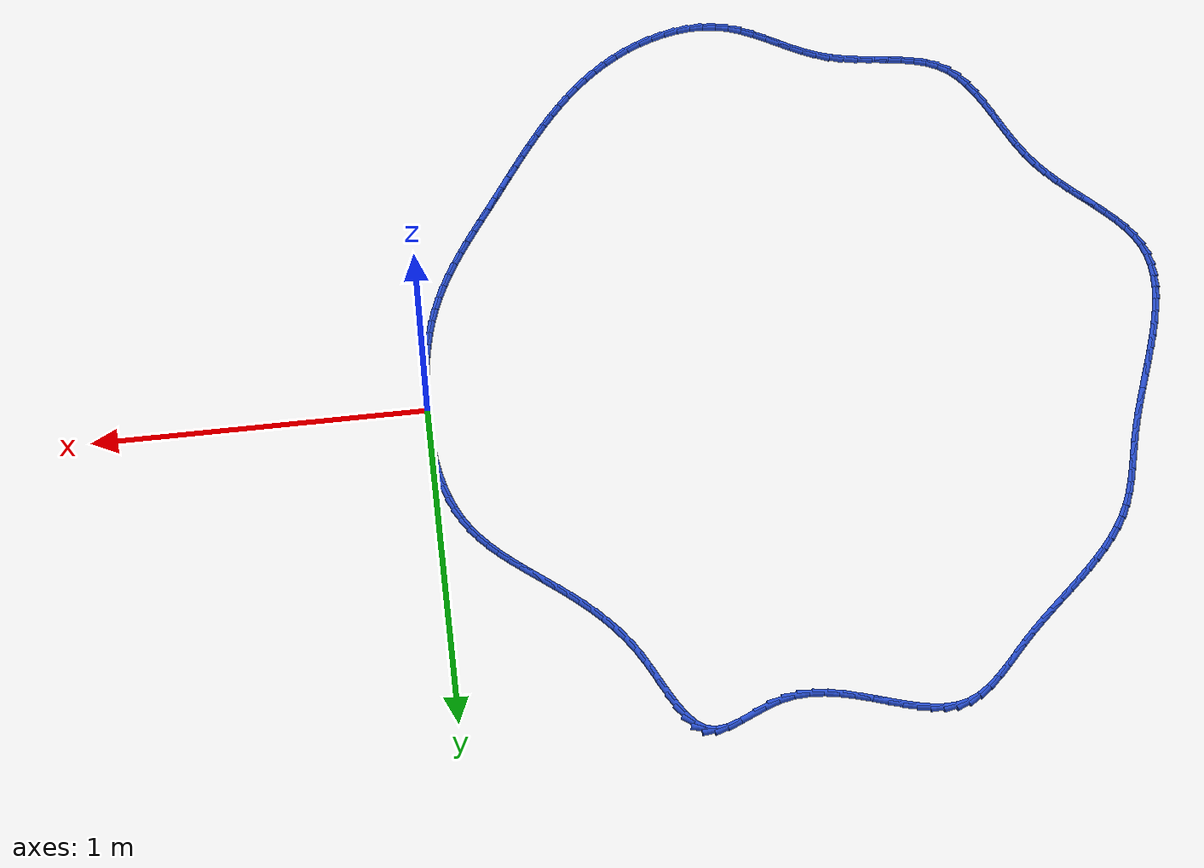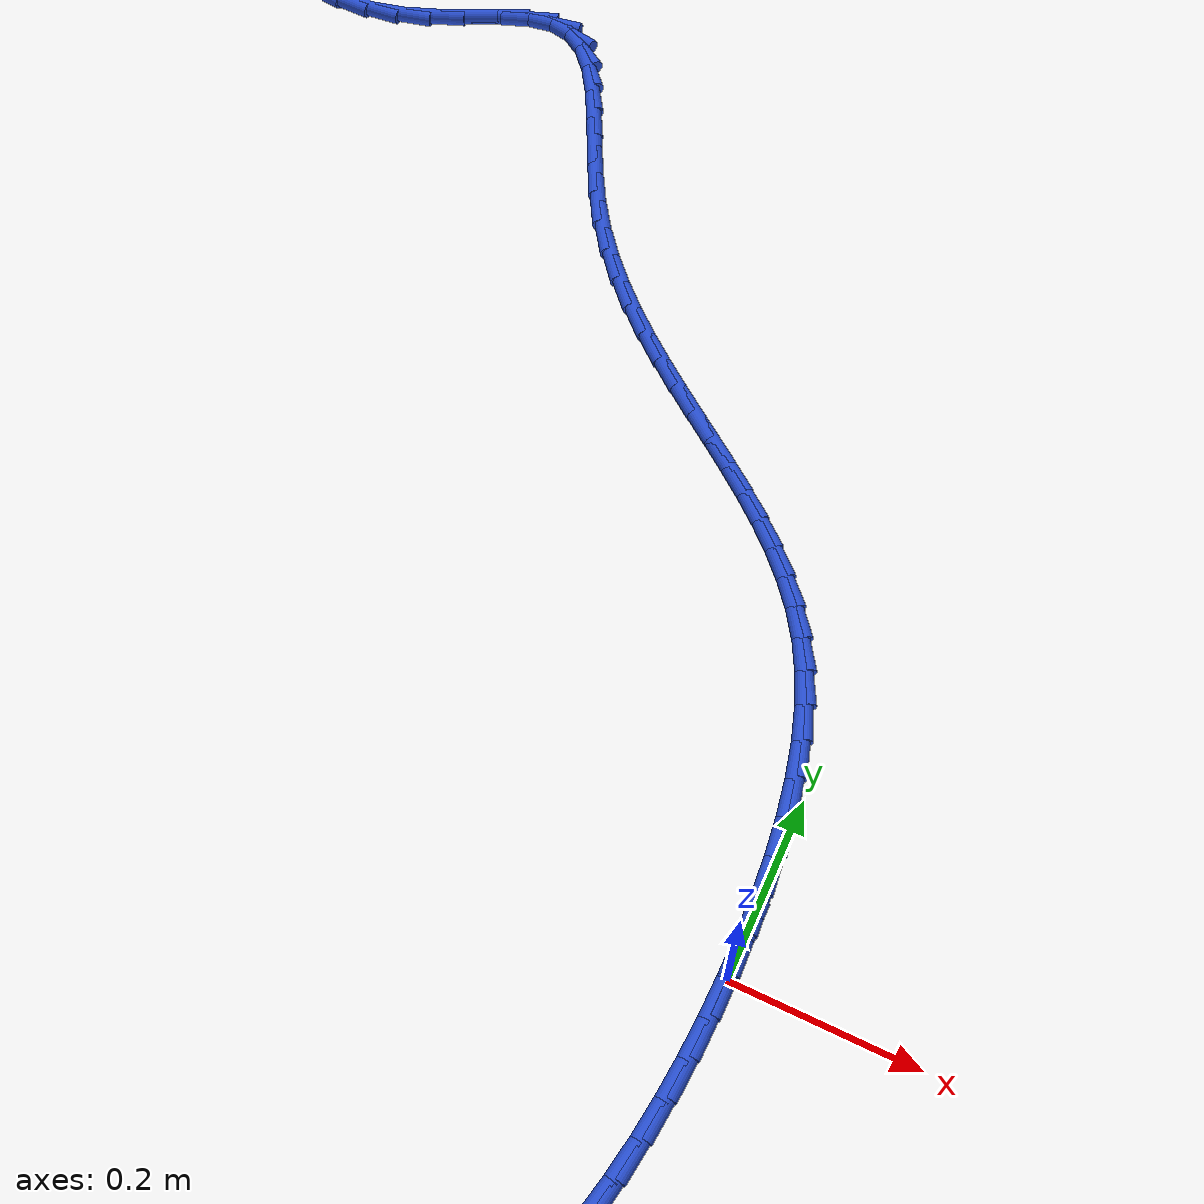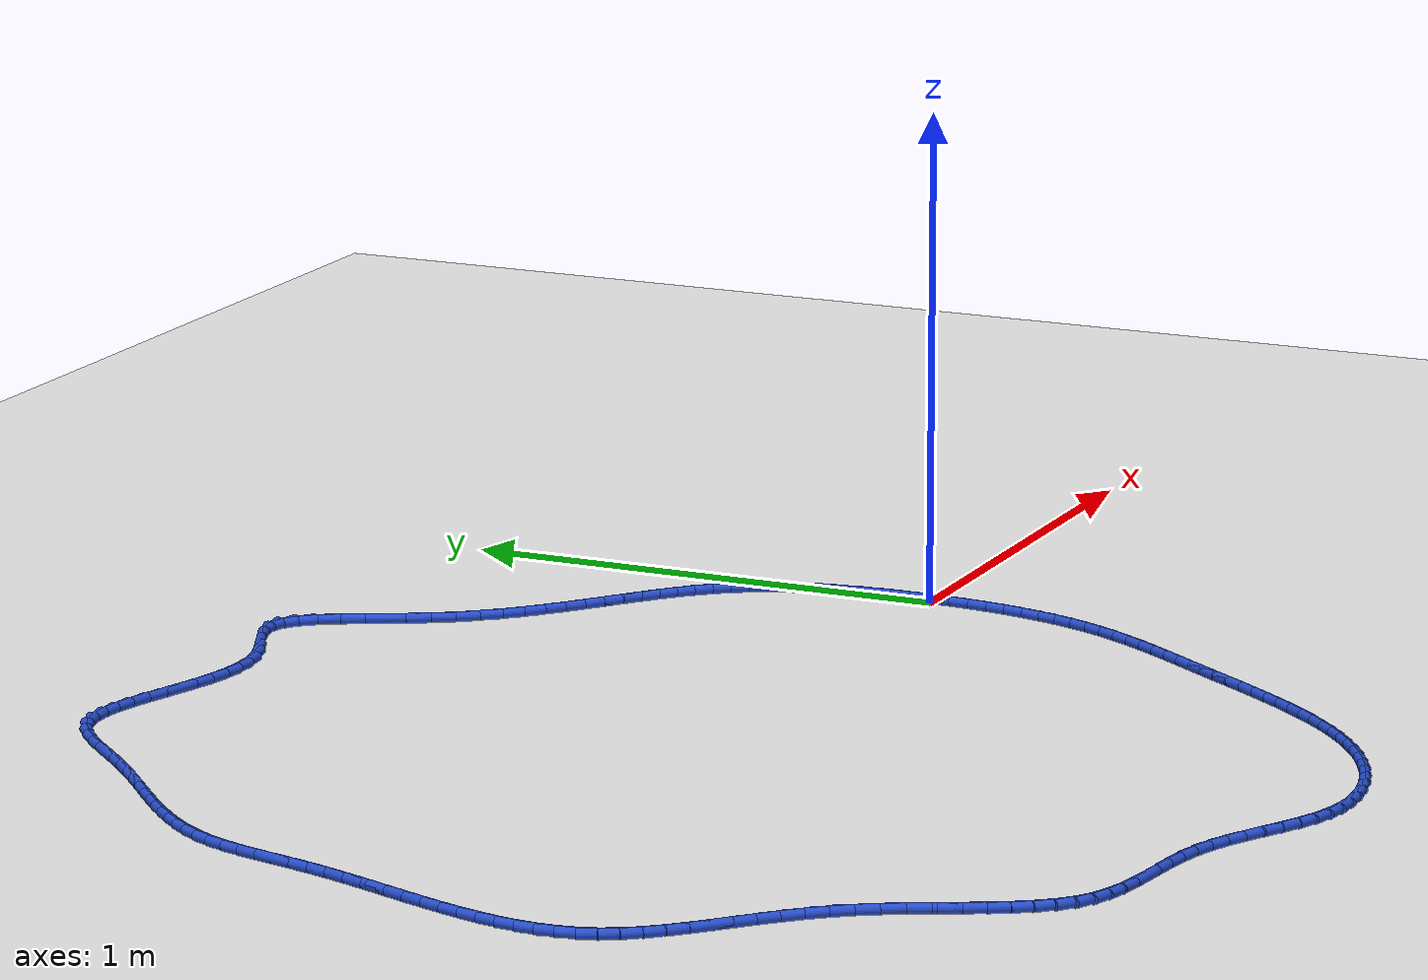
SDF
<sdf version="1.6">
 <world name="default">
  <light name="sun" type="directional">
   <pose>0 0 10 0 -0 0</pose>
   <diffuse>0.8 0.8 0.8 1</diffuse>
   <specular>0.2 0.2 0.2 1</specular>
   <attenuation>
    <range>1000</range>
    <constant>0.9</constant>
    <linear>0.01</linear>
    <quadratic>0.001</quadratic>
   </attenuation>
   <direction>-0.5 0.1 -0.9</direction>
  </light>
  <model name="ground_plane">
   <static>1</static>
   <link name="link">
    <collision name="collision">
     <geometry><plane><normal>0 0 1</normal><size>100 100</size></plane></geometry>
     <surface><friction><ode><mu>100</mu><mu2>50</mu2></ode></friction></surface>
    </collision>
    <visual name="visual">
     <cast_shadows>0</cast_shadows>
     <geometry><plane><normal>0 0 1</normal><size>100 100</size></plane></geometry>
     <material>
      <script><uri>file://media/materials/scripts/gazebo.material</uri><name>Gazebo/WhiteGlow</name></script>
     </material>
    </visual>
   </link>
  </model>
  <gravity>0 0 -9.8</gravity>
  <magnetic_field>6e-06 2.3e-05 -4.2e-05</magnetic_field>
  <atmosphere type="adiabatic"/>
  <physics name="default_physics" default="0" type="ode">
   <max_step_size>0.001</max_step_size>
   <real_time_factor>1</real_time_factor>
   <real_time_update_rate>1000</real_time_update_rate>
  </physics>
  <scene><ambient>0.4 0.4 0.4 1</ambient><background>0.7 0.7 0.7 1</background><shadows>1</shadows></scene>
  <spherical_coordinates>
   <surface_model>EARTH_WGS84</surface_model>
   <latitude_deg>0</latitude_deg>
   <longitude_deg>0</longitude_deg>
   <elevation>0</elevation>
   <heading_deg>0</heading_deg>
  </spherical_coordinates>
  <model name="line">
   <link name="link_0">
    <pose>-2.0816681711721685e-17 -4.163336342344337e-17 0.01 0 1.57 1.5702405880663068</pose>
    <collision name="collision">
     <geometry><cylinder><radius>0.01</radius><length>0.08</length></cylinder></geometry>
    </collision>
    <visual name="visual">
     <material>
      <script><name>Gazebo/Blue</name><uri>file://media/materials/scripts/gazebo.material</uri></script>
     </material>
     <geometry><cylinder><radius>0.01</radius><length>0.08</length></cylinder></geometry>
    </visual>
   </link>
   <link name="link_1">
    <pose>2.4101611619804057e-05 0.04336859732587032 0.01 0 1.57 -1.5373935220403587</pose>
    <collision name="collision">
     <geometry><cylinder><radius>0.01</radius><length>0.08</length></cylinder></geometry>
    </collision>
    <visual name="visual">
     <material>
      <script><name>Gazebo/Blue</name><uri>file://media/materials/scripts/gazebo.material</uri></script>
     </material>
     <geometry><cylinder><radius>0.01</radius><length>0.08</length></cylinder></geometry>
    </visual>
   </link>
   <link name="link_2">
    <pose>-0.001427749246306789 0.08681736943247514 0.01 0 1.57 -1.4984947802838482</pose>
    <collision name="collision">
     <geometry><cylinder><radius>0.01</radius><length>0.08</length></cylinder></geometry>
    </collision>
    <visual name="visual">
     <material>
      <script><name>Gazebo/Blue</name><uri>file://media/materials/scripts/gazebo.material</uri></script>
     </material>
     <geometry><cylinder><radius>0.01</radius><length>0.08</length></cylinder></geometry>
    </visual>
   </link>
   <link name="link_3">
    <pose>-0.004556395814565118 0.13001413543887705 0.01 0 1.57 -1.4538486660586079</pose>
    <collision name="collision">
     <geometry><cylinder><radius>0.01</radius><length>0.08</length></cylinder></geometry>
    </collision>
    <visual name="visual">
     <material>
      <script><name>Gazebo/Blue</name><uri>file://media/materials/scripts/gazebo.material</uri></script>
     </material>
     <geometry><cylinder><radius>0.01</radius><length>0.08</length></cylinder></geometry>
    </visual>
   </link>
   <link name="link_4">
    <pose>-0.009562681333940507 0.1726267144641387 0.01 0 1.57 -1.4024898091452374</pose>
    <collision name="collision">
     <geometry><cylinder><radius>0.01</radius><length>0.08</length></cylinder></geometry>
    </collision>
    <visual name="visual">
     <material>
      <script><name>Gazebo/Blue</name><uri>file://media/materials/scripts/gazebo.material</uri></script>
     </material>
     <geometry><cylinder><radius>0.01</radius><length>0.08</length></cylinder></geometry>
    </visual>
   </link>
   <link name="link_5">
    <pose>-0.016647449045218282 0.2143229256273228 0.01 0 1.57 -1.343292992065598</pose>
    <collision name="collision">
     <geometry><cylinder><radius>0.01</radius><length>0.08</length></cylinder></geometry>
    </collision>
    <visual name="visual">
     <material>
      <script><name>Gazebo/Blue</name><uri>file://media/materials/scripts/gazebo.material</uri></script>
     </material>
     <geometry><cylinder><radius>0.01</radius><length>0.08</length></cylinder></geometry>
    </visual>
   </link>
   <link name="link_6">
    <pose>-0.02601154218918376 0.254770588047492 0.01 0 1.57 -1.274997714693162</pose>
    <collision name="collision">
     <geometry><cylinder><radius>0.01</radius><length>0.08</length></cylinder></geometry>
    </collision>
    <visual name="visual">
     <material>
      <script><name>Gazebo/Blue</name><uri>file://media/materials/scripts/gazebo.material</uri></script>
     </material>
     <geometry><cylinder><radius>0.01</radius><length>0.08</length></cylinder></geometry>
    </visual>
   </link>
   <link name="link_7">
    <pose>-0.03785580400662226 0.2936375208437088 0.01 0 1.57 -1.196284041089661</pose>
    <collision name="collision">
     <geometry><cylinder><radius>0.01</radius><length>0.08</length></cylinder></geometry>
    </collision>
    <visual name="visual">
     <material>
      <script><name>Gazebo/Blue</name><uri>file://media/materials/scripts/gazebo.material</uri></script>
     </material>
     <geometry><cylinder><radius>0.01</radius><length>0.08</length></cylinder></geometry>
    </visual>
   </link>
   <link name="link_8">
    <pose>-0.052381077738319105 0.33059154313503614 0.01 0 1.57 -1.1059415740129674</pose>
    <collision name="collision">
     <geometry><cylinder><radius>0.01</radius><length>0.08</length></cylinder></geometry>
    </collision>
    <visual name="visual">
     <material>
      <script><name>Gazebo/Blue</name><uri>file://media/materials/scripts/gazebo.material</uri></script>
     </material>
     <geometry><cylinder><radius>0.01</radius><length>0.08</length></cylinder></geometry>
    </visual>
   </link>
   <link name="link_9">
    <pose>-0.0697880516994772 0.36530068044756714 0.01 0 1.57 -1.0081884148373188</pose>
    <collision name="collision">
     <geometry><cylinder><radius>0.01</radius><length>0.08</length></cylinder></geometry>
    </collision>
    <visual name="visual">
     <material>
      <script><name>Gazebo/Blue</name><uri>file://media/materials/scripts/gazebo.material</uri></script>
     </material>
     <geometry><cylinder><radius>0.01</radius><length>0.08</length></cylinder></geometry>
    </visual>
   </link>
   <link name="link_10">
    <pose>-0.09015398931109625 0.39759739703677704 0.01 0 1.57 -0.918357097890116</pose>
    <collision name="collision">
     <geometry><cylinder><radius>0.01</radius><length>0.08</length></cylinder></geometry>
    </collision>
    <visual name="visual">
     <material>
      <script><name>Gazebo/Blue</name><uri>file://media/materials/scripts/gazebo.material</uri></script>
     </material>
     <geometry><cylinder><radius>0.01</radius><length>0.08</length></cylinder></geometry>
    </visual>
   </link>
   <link name="link_11">
    <pose>-0.11321087206196469 0.42777417555700514 0.01 0 1.57 -0.8412233249746979</pose>
    <collision name="collision">
     <geometry><cylinder><radius>0.01</radius><length>0.08</length></cylinder></geometry>
    </collision>
    <visual name="visual">
     <material>
      <script><name>Gazebo/Blue</name><uri>file://media/materials/scripts/gazebo.material</uri></script>
     </material>
     <geometry><cylinder><radius>0.01</radius><length>0.08</length></cylinder></geometry>
    </visual>
   </link>
   <link name="link_12">
    <pose>-0.1386307643505817 0.45620332607714176 0.01 0 1.57 -0.7780392341299396</pose>
    <collision name="collision">
     <geometry><cylinder><radius>0.01</radius><length>0.08</length></cylinder></geometry>
    </collision>
    <visual name="visual">
     <material>
      <script><name>Gazebo/Blue</name><uri>file://media/materials/scripts/gazebo.material</uri></script>
     </material>
     <geometry><cylinder><radius>0.01</radius><length>0.08</length></cylinder></geometry>
    </visual>
   </link>
   <link name="link_13">
    <pose>-0.16608573057544626 0.483257158666077 0.01 0 1.57 -0.7291071286449811</pose>
    <collision name="collision">
     <geometry><cylinder><radius>0.01</radius><length>0.08</length></cylinder></geometry>
    </collision>
    <visual name="visual">
     <material>
      <script><name>Gazebo/Blue</name><uri>file://media/materials/scripts/gazebo.material</uri></script>
     </material>
     <geometry><cylinder><radius>0.01</radius><length>0.08</length></cylinder></geometry>
    </visual>
   </link>
   <link name="link_14">
    <pose>-0.19524783513505736 0.5093079833927008 0.01 0 1.57 -0.6941396754114768</pose>
    <collision name="collision">
     <geometry><cylinder><radius>0.01</radius><length>0.08</length></cylinder></geometry>
    </collision>
    <visual name="visual">
     <material>
      <script><name>Gazebo/Blue</name><uri>file://media/materials/scripts/gazebo.material</uri></script>
     </material>
     <geometry><cylinder><radius>0.01</radius><length>0.08</length></cylinder></geometry>
    </visual>
   </link>
   <link name="link_15">
    <pose>-0.22578914242791417 0.5347281103259036 0.01 0 1.57 -0.6725693280413313</pose>
    <collision name="collision">
     <geometry><cylinder><radius>0.01</radius><length>0.08</length></cylinder></geometry>
    </collision>
    <visual name="visual">
     <material>
      <script><name>Gazebo/Blue</name><uri>file://media/materials/scripts/gazebo.material</uri></script>
     </material>
     <geometry><cylinder><radius>0.01</radius><length>0.08</length></cylinder></geometry>
    </visual>
   </link>
   <link name="link_16">
    <pose>-0.25738171685251576 0.5598898495345754 0.01 0 1.57 -0.663757326702378</pose>
    <collision name="collision">
     <geometry><cylinder><radius>0.01</radius><length>0.08</length></cylinder></geometry>
    </collision>
    <visual name="visual">
     <material>
      <script><name>Gazebo/Blue</name><uri>file://media/materials/scripts/gazebo.material</uri></script>
     </material>
     <geometry><cylinder><radius>0.01</radius><length>0.08</length></cylinder></geometry>
    </visual>
   </link>
   <link name="link_17">
    <pose>-0.28969762280736117 0.5851655110876065 0.01 0 1.57 -0.6671052822627369</pose>
    <collision name="collision">
     <geometry><cylinder><radius>0.01</radius><length>0.08</length></cylinder></geometry>
    </collision>
    <visual name="visual">
     <material>
      <script><name>Gazebo/Blue</name><uri>file://media/materials/scripts/gazebo.material</uri></script>
     </material>
     <geometry><cylinder><radius>0.01</radius><length>0.08</length></cylinder></geometry>
    </visual>
   </link>
   <link name="link_18">
    <pose>-0.32240892469094934 0.610927405053887 0.01 0 1.57 -0.6820903403879932</pose>
    <collision name="collision">
     <geometry><cylinder><radius>0.01</radius><length>0.08</length></cylinder></geometry>
    </collision>
    <visual name="visual">
     <material>
      <script><name>Gazebo/Blue</name><uri>file://media/materials/scripts/gazebo.material</uri></script>
     </material>
     <geometry><cylinder><radius>0.01</radius><length>0.08</length></cylinder></geometry>
    </visual>
   </link>
   <link name="link_19">
    <pose>-0.3551876869017795 0.6375478415023073 0.01 0 1.57 -0.7082445012371428</pose>
    <collision name="collision">
     <geometry><cylinder><radius>0.01</radius><length>0.08</length></cylinder></geometry>
    </collision>
    <visual name="visual">
     <material>
      <script><name>Gazebo/Blue</name><uri>file://media/materials/scripts/gazebo.material</uri></script>
     </material>
     <geometry><cylinder><radius>0.01</radius><length>0.08</length></cylinder></geometry>
    </visual>
   </link>
   <link name="link_20">
    <pose>-0.3877059738383508 0.6653991305017571 0.01 0 1.57 -0.7450933500096423</pose>
    <collision name="collision">
     <geometry><cylinder><radius>0.01</radius><length>0.08</length></cylinder></geometry>
    </collision>
    <visual name="visual">
     <material>
      <script><name>Gazebo/Blue</name><uri>file://media/materials/scripts/gazebo.material</uri></script>
     </material>
     <geometry><cylinder><radius>0.01</radius><length>0.08</length></cylinder></geometry>
    </visual>
   </link>
   <link name="link_21">
    <pose>-0.41963584989916203 0.694853582121127 0.01 0 1.57 -0.7920664132606304</pose>
    <collision name="collision">
     <geometry><cylinder><radius>0.01</radius><length>0.08</length></cylinder></geometry>
    </collision>
    <visual name="visual">
     <material>
      <script><name>Gazebo/Blue</name><uri>file://media/materials/scripts/gazebo.material</uri></script>
     </material>
     <geometry><cylinder><radius>0.01</radius><length>0.08</length></cylinder></geometry>
    </visual>
   </link>
   <link name="link_22">
    <pose>-0.45064937948271205 0.7262835064293065 0.01 0 1.57 -0.8483934051655299</pose>
    <collision name="collision">
     <geometry><cylinder><radius>0.01</radius><length>0.08</length></cylinder></geometry>
    </collision>
    <visual name="visual">
     <material>
      <script><name>Gazebo/Blue</name><uri>file://media/materials/scripts/gazebo.material</uri></script>
     </material>
     <geometry><cylinder><radius>0.01</radius><length>0.08</length></cylinder></geometry>
    </visual>
   </link>
   <link name="link_23">
    <pose>-0.4804186269875006 0.7600612134951867 0.01 0 1.57 -0.9130074969552721</pose>
    <collision name="collision">
     <geometry><cylinder><radius>0.01</radius><length>0.08</length></cylinder></geometry>
    </collision>
    <visual name="visual">
     <material>
      <script><name>Gazebo/Blue</name><uri>file://media/materials/scripts/gazebo.material</uri></script>
     </material>
     <geometry><cylinder><radius>0.01</radius><length>0.08</length></cylinder></geometry>
    </visual>
   </link>
   <link name="link_24">
    <pose>-0.5086156568120264 0.7965590133876577 0.01 0 1.57 -0.9844847147053257</pose>
    <collision name="collision">
     <geometry><cylinder><radius>0.01</radius><length>0.08</length></cylinder></geometry>
    </collision>
    <visual name="visual">
     <material>
      <script><name>Gazebo/Blue</name><uri>file://media/materials/scripts/gazebo.material</uri></script>
     </material>
     <geometry><cylinder><radius>0.01</radius><length>0.08</length></cylinder></geometry>
    </visual>
   </link>
   <link name="link_25">
    <pose>-0.5349125333547884 0.8361492161756088 0.01 0 1.57 -1.056377052260185</pose>
    <collision name="collision">
     <geometry><cylinder><radius>0.01</radius><length>0.08</length></cylinder></geometry>
    </collision>
    <visual name="visual">
     <material>
      <script><name>Gazebo/Blue</name><uri>file://media/materials/scripts/gazebo.material</uri></script>
     </material>
     <geometry><cylinder><radius>0.01</radius><length>0.08</length></cylinder></geometry>
    </visual>
   </link>
   <link name="link_26">
    <pose>-0.5590979915514123 0.8789420735021811 0.01 0 1.57 -1.1002546652539384</pose>
    <collision name="collision">
     <geometry><cylinder><radius>0.01</radius><length>0.08</length></cylinder></geometry>
    </collision>
    <visual name="visual">
     <material>
      <script><name>Gazebo/Blue</name><uri>file://media/materials/scripts/gazebo.material</uri></script>
     </material>
     <geometry><cylinder><radius>0.01</radius><length>0.08</length></cylinder></geometry>
    </visual>
   </link>
   <link name="link_27">
    <pose>-0.581702335370363 0.9233821687268409 0.01 0 1.57 -1.1088985701030307</pose>
    <collision name="collision">
     <geometry><cylinder><radius>0.01</radius><length>0.08</length></cylinder></geometry>
    </collision>
    <visual name="visual">
     <material>
      <script><name>Gazebo/Blue</name><uri>file://media/materials/scripts/gazebo.material</uri></script>
     </material>
     <geometry><cylinder><radius>0.01</radius><length>0.08</length></cylinder></geometry>
    </visual>
   </link>
   <link name="link_28">
    <pose>-0.6035462642569058 0.9672618161497943 0.01 0 1.57 -1.0812261580175133</pose>
    <collision name="collision">
     <geometry><cylinder><radius>0.01</radius><length>0.08</length></cylinder></geometry>
    </collision>
    <visual name="visual">
     <material>
      <script><name>Gazebo/Blue</name><uri>file://media/materials/scripts/gazebo.material</uri></script>
     </material>
     <geometry><cylinder><radius>0.01</radius><length>0.08</length></cylinder></geometry>
    </visual>
   </link>
   <link name="link_29">
    <pose>-0.6254511547932186 1.0083718091265603 0.01 0 1.57 -1.0081220190441231</pose>
    <collision name="collision">
     <geometry><cylinder><radius>0.01</radius><length>0.08</length></cylinder></geometry>
    </collision>
    <visual name="visual">
     <material>
      <script><name>Gazebo/Blue</name><uri>file://media/materials/scripts/gazebo.material</uri></script>
     </material>
     <geometry><cylinder><radius>0.01</radius><length>0.08</length></cylinder></geometry>
    </visual>
   </link>
   <link name="link_30">
    <pose>-0.6482383835614794 1.0445029410126594 0.01 0 1.57 -0.8685261361282299</pose>
    <collision name="collision">
     <geometry><cylinder><radius>0.01</radius><length>0.08</length></cylinder></geometry>
    </collision>
    <visual name="visual">
     <material>
      <script><name>Gazebo/Blue</name><uri>file://media/materials/scripts/gazebo.material</uri></script>
     </material>
     <geometry><cylinder><radius>0.01</radius><length>0.08</length></cylinder></geometry>
    </visual>
   </link>
   <link name="link_31">
    <pose>-0.6727293271438661 1.0734460051636106 0.01 0 1.57 -0.6263167182668777</pose>
    <collision name="collision">
     <geometry><cylinder><radius>0.01</radius><length>0.08</length></cylinder></geometry>
    </collision>
    <visual name="visual">
     <material>
      <script><name>Gazebo/Blue</name><uri>file://media/materials/scripts/gazebo.material</uri></script>
     </material>
     <geometry><cylinder><radius>0.01</radius><length>0.08</length></cylinder></geometry>
    </visual>
   </link>
   <link name="link_32">
    <pose>-0.6997453621225573 1.092991794934934 0.01 0 1.57 -0.2558869594768532</pose>
    <collision name="collision">
     <geometry><cylinder><radius>0.01</radius><length>0.08</length></cylinder></geometry>
    </collision>
    <visual name="visual">
     <material>
      <script><name>Gazebo/Blue</name><uri>file://media/materials/scripts/gazebo.material</uri></script>
     </material>
     <geometry><cylinder><radius>0.01</radius><length>0.08</length></cylinder></geometry>
    </visual>
   </link>
   <link name="link_33">
    <pose>-0.7301069069934344 1.100935049722213 0.01 0 1.57 0.12470405745999866</pose>
    <collision name="collision">
     <geometry><cylinder><radius>0.01</radius><length>0.08</length></cylinder></geometry>
    </collision>
    <visual name="visual">
     <material>
      <script><name>Gazebo/Blue</name><uri>file://media/materials/scripts/gazebo.material</uri></script>
     </material>
     <geometry><cylinder><radius>0.01</radius><length>0.08</length></cylinder></geometry>
    </visual>
   </link>
   <link name="link_34">
    <pose>-0.7642496458045249 1.096655102660111 0.01 0 1.57 0.3375328449752318</pose>
    <collision name="collision">
     <geometry><cylinder><radius>0.01</radius><length>0.08</length></cylinder></geometry>
    </collision>
    <visual name="visual">
     <material>
      <script><name>Gazebo/Blue</name><uri>file://media/materials/scripts/gazebo.material</uri></script>
     </material>
     <geometry><cylinder><radius>0.01</radius><length>0.08</length></cylinder></geometry>
    </visual>
   </link>
   <link name="link_35">
    <pose>-0.8016375854017671 1.0835333033895214 0.01 0 1.57 0.42253069600633086</pose>
    <collision name="collision">
     <geometry><cylinder><radius>0.01</radius><length>0.08</length></cylinder></geometry>
    </collision>
    <visual name="visual">
     <material>
      <script><name>Gazebo/Blue</name><uri>file://media/materials/scripts/gazebo.material</uri></script>
     </material>
     <geometry><cylinder><radius>0.01</radius><length>0.08</length></cylinder></geometry>
    </visual>
   </link>
   <link name="link_36">
    <pose>-0.8415836942596983 1.065573078568401 0.01 0 1.57 0.42240564750308596</pose>
    <collision name="collision">
     <geometry><cylinder><radius>0.01</radius><length>0.08</length></cylinder></geometry>
    </collision>
    <visual name="visual">
     <material>
      <script><name>Gazebo/Blue</name><uri>file://media/materials/scripts/gazebo.material</uri></script>
     </material>
     <geometry><cylinder><radius>0.01</radius><length>0.08</length></cylinder></geometry>
    </visual>
   </link>
   <link name="link_37">
    <pose>-0.8834009408528556 1.0467778548547073 0.01 0 1.57 0.34856437198829776</pose>
    <collision name="collision">
     <geometry><cylinder><radius>0.01</radius><length>0.08</length></cylinder></geometry>
    </collision>
    <visual name="visual">
     <material>
      <script><name>Gazebo/Blue</name><uri>file://media/materials/scripts/gazebo.material</uri></script>
     </material>
     <geometry><cylinder><radius>0.01</radius><length>0.08</length></cylinder></geometry>
    </visual>
   </link>
   <link name="link_38">
    <pose>-0.9264022936557758 1.0311510589063975 0.01 0 1.57 0.2041113422869888</pose>
    <collision name="collision">
     <geometry><cylinder><radius>0.01</radius><length>0.08</length></cylinder></geometry>
    </collision>
    <visual name="visual">
     <material>
      <script><name>Gazebo/Blue</name><uri>file://media/materials/scripts/gazebo.material</uri></script>
     </material>
     <geometry><cylinder><radius>0.01</radius><length>0.08</length></cylinder></geometry>
    </visual>
   </link>
   <link name="link_39">
    <pose>-0.9699560365664643 1.0221356992442234 0.01 0 1.57 0.053309065515965266</pose>
    <collision name="collision">
     <geometry><cylinder><radius>0.01</radius><length>0.08</length></cylinder></geometry>
    </collision>
    <visual name="visual">
     <material>
      <script><name>Gazebo/Blue</name><uri>file://media/materials/scripts/gazebo.material</uri></script>
     </material>
     <geometry><cylinder><radius>0.01</radius><length>0.08</length></cylinder></geometry>
    </visual>
   </link>
   <link name="link_40">
    <pose>-1.013763741587224 1.0197981366684248 0.01 0 1.57 -0.07160802732899497</pose>
    <collision name="collision">
     <geometry><cylinder><radius>0.01</radius><length>0.08</length></cylinder></geometry>
    </collision>
    <visual name="visual">
     <material>
      <script><name>Gazebo/Blue</name><uri>file://media/materials/scripts/gazebo.material</uri></script>
     </material>
     <geometry><cylinder><radius>0.01</radius><length>0.08</length></cylinder></geometry>
    </visual>
   </link>
   <link name="link_41">
    <pose>-1.0576512013070305 1.0229462137320582 0.01 0 1.57 -0.16826974715867132</pose>
    <collision name="collision">
     <geometry><cylinder><radius>0.01</radius><length>0.08</length></cylinder></geometry>
    </collision>
    <visual name="visual">
     <material>
      <script><name>Gazebo/Blue</name><uri>file://media/materials/scripts/gazebo.material</uri></script>
     </material>
     <geometry><cylinder><radius>0.01</radius><length>0.08</length></cylinder></geometry>
    </visual>
   </link>
   <link name="link_42">
    <pose>-1.101444419306156 1.030385635368277 0.01 0 1.57 -0.2375095524006145</pose>
    <collision name="collision">
     <geometry><cylinder><radius>0.01</radius><length>0.08</length></cylinder></geometry>
    </collision>
    <visual name="visual">
     <material>
      <script><name>Gazebo/Blue</name><uri>file://media/materials/scripts/gazebo.material</uri></script>
     </material>
     <geometry><cylinder><radius>0.01</radius><length>0.08</length></cylinder></geometry>
    </visual>
   </link>
   <link name="link_43">
    <pose>-1.1449693991648742 1.0409221065102345 0.01 0 1.57 -0.2810843573207855</pose>
    <collision name="collision">
     <geometry><cylinder><radius>0.01</radius><length>0.08</length></cylinder></geometry>
    </collision>
    <visual name="visual">
     <material>
      <script><name>Gazebo/Blue</name><uri>file://media/materials/scripts/gazebo.material</uri></script>
     </material>
     <geometry><cylinder><radius>0.01</radius><length>0.08</length></cylinder></geometry>
    </visual>
   </link>
   <link name="link_44">
    <pose>-1.1880521444634573 1.0533613320910835 0.01 0 1.57 -0.30024181852711873</pose>
    <collision name="collision">
     <geometry><cylinder><radius>0.01</radius><length>0.08</length></cylinder></geometry>
    </collision>
    <visual name="visual">
     <material>
      <script><name>Gazebo/Blue</name><uri>file://media/materials/scripts/gazebo.material</uri></script>
     </material>
     <geometry><cylinder><radius>0.01</radius><length>0.08</length></cylinder></geometry>
    </visual>
   </link>
   <link name="link_45">
    <pose>-1.23051865878218 1.0665090170439782 0.01 0 1.57 -0.2949524093925511</pose>
    <collision name="collision">
     <geometry><cylinder><radius>0.01</radius><length>0.08</length></cylinder></geometry>
    </collision>
    <visual name="visual">
     <material>
      <script><name>Gazebo/Blue</name><uri>file://media/materials/scripts/gazebo.material</uri></script>
     </material>
     <geometry><cylinder><radius>0.01</radius><length>0.08</length></cylinder></geometry>
    </visual>
   </link>
   <link name="link_46">
    <pose>-1.272194945701314 1.0791708663020705 0.01 0 1.57 -0.26347055164437866</pose>
    <collision name="collision">
     <geometry><cylinder><radius>0.01</radius><length>0.08</length></cylinder></geometry>
    </collision>
    <visual name="visual">
     <material>
      <script><name>Gazebo/Blue</name><uri>file://media/materials/scripts/gazebo.material</uri></script>
     </material>
     <geometry><cylinder><radius>0.01</radius><length>0.08</length></cylinder></geometry>
    </visual>
   </link>
   <link name="link_47">
    <pose>-1.3129070088011332 1.0901525847985147 0.01 0 1.57 -0.2020689737502055</pose>
    <collision name="collision">
     <geometry><cylinder><radius>0.01</radius><length>0.08</length></cylinder></geometry>
    </collision>
    <visual name="visual">
     <material>
      <script><name>Gazebo/Blue</name><uri>file://media/materials/scripts/gazebo.material</uri></script>
     </material>
     <geometry><cylinder><radius>0.01</radius><length>0.08</length></cylinder></geometry>
    </visual>
   </link>
   <link name="link_48">
    <pose>-1.3524808516619096 1.0982598774664631 0.01 0 1.57 -0.10516210549216867</pose>
    <collision name="collision">
     <geometry><cylinder><radius>0.01</radius><length>0.08</length></cylinder></geometry>
    </collision>
    <visual name="visual">
     <material>
      <script><name>Gazebo/Blue</name><uri>file://media/materials/scripts/gazebo.material</uri></script>
     </material>
     <geometry><cylinder><radius>0.01</radius><length>0.08</length></cylinder></geometry>
    </visual>
   </link>
   <link name="link_49">
    <pose>-1.3907424778639172 1.1022984492390697 0.01 0 1.57 0.03328289000447437</pose>
    <collision name="collision">
     <geometry><cylinder><radius>0.01</radius><length>0.08</length></cylinder></geometry>
    </collision>
    <visual name="visual">
     <material>
      <script><name>Gazebo/Blue</name><uri>file://media/materials/scripts/gazebo.material</uri></script>
     </material>
     <geometry><cylinder><radius>0.01</radius><length>0.08</length></cylinder></geometry>
    </visual>
   </link>
   <link name="link_50">
    <pose>-1.4275178909874298 1.1010740050494876 0.01 0 1.57 0.21536597312415923</pose>
    <collision name="collision">
     <geometry><cylinder><radius>0.01</radius><length>0.08</length></cylinder></geometry>
    </collision>
    <visual name="visual">
     <material>
      <script><name>Gazebo/Blue</name><uri>file://media/materials/scripts/gazebo.material</uri></script>
     </material>
     <geometry><cylinder><radius>0.01</radius><length>0.08</length></cylinder></geometry>
    </visual>
   </link>
   <link name="link_51">
    <pose>-1.4626330946127184 1.0933922498308692 0.01 0 1.57 0.42525330479596446</pose>
    <collision name="collision">
     <geometry><cylinder><radius>0.01</radius><length>0.08</length></cylinder></geometry>
    </collision>
    <visual name="visual">
     <material>
      <script><name>Gazebo/Blue</name><uri>file://media/materials/scripts/gazebo.material</uri></script>
     </material>
     <geometry><cylinder><radius>0.01</radius><length>0.08</length></cylinder></geometry>
    </visual>
   </link>
   <link name="link_52">
    <pose>-1.4959683960452996 1.0782950792674386 0.01 0 1.57 0.5995593160627108</pose>
    <collision name="collision">
     <geometry><cylinder><radius>0.01</radius><length>0.08</length></cylinder></geometry>
    </collision>
    <visual name="visual">
     <material>
      <script><name>Gazebo/Blue</name><uri>file://media/materials/scripts/gazebo.material</uri></script>
     </material>
     <geometry><cylinder><radius>0.01</radius><length>0.08</length></cylinder></geometry>
    </visual>
   </link>
   <link name="link_53">
    <pose>-1.527798444963173 1.0565395572150778 0.01 0 1.57 0.7183330386621934</pose>
    <collision name="collision">
     <geometry><cylinder><radius>0.01</radius><length>0.08</length></cylinder></geometry>
    </collision>
    <visual name="visual">
     <material>
      <script><name>Gazebo/Blue</name><uri>file://media/materials/scripts/gazebo.material</uri></script>
     </material>
     <geometry><cylinder><radius>0.01</radius><length>0.08</length></cylinder></geometry>
    </visual>
   </link>
   <link name="link_54">
    <pose>-1.5585719355098746 1.0296397433499664 0.01 0 1.57 0.7913349928397684</pose>
    <collision name="collision">
     <geometry><cylinder><radius>0.01</radius><length>0.08</length></cylinder></geometry>
    </collision>
    <visual name="visual">
     <material>
      <script><name>Gazebo/Blue</name><uri>file://media/materials/scripts/gazebo.material</uri></script>
     </material>
     <geometry><cylinder><radius>0.01</radius><length>0.08</length></cylinder></geometry>
    </visual>
   </link>
   <link name="link_55">
    <pose>-1.5887383265448374 0.9991130234335746 0.01 0 1.57 0.8273161313582819</pose>
    <collision name="collision">
     <geometry><cylinder><radius>0.01</radius><length>0.08</length></cylinder></geometry>
    </collision>
    <visual name="visual">
     <material>
      <script><name>Gazebo/Blue</name><uri>file://media/materials/scripts/gazebo.material</uri></script>
     </material>
     <geometry><cylinder><radius>0.01</radius><length>0.08</length></cylinder></geometry>
    </visual>
   </link>
   <link name="link_56">
    <pose>-1.6187470769274908 0.966476783227372 0.01 0 1.57 0.8314517541729631</pose>
    <collision name="collision">
     <geometry><cylinder><radius>0.01</radius><length>0.08</length></cylinder></geometry>
    </collision>
    <visual name="visual">
     <material>
      <script><name>Gazebo/Blue</name><uri>file://media/materials/scripts/gazebo.material</uri></script>
     </material>
     <geometry><cylinder><radius>0.01</radius><length>0.08</length></cylinder></geometry>
    </visual>
   </link>
   <link name="link_57">
    <pose>-1.6490476455172673 0.9332484084928288 0.01 0 1.57 0.8074483909060773</pose>
    <collision name="collision">
     <geometry><cylinder><radius>0.01</radius><length>0.08</length></cylinder></geometry>
    </collision>
    <visual name="visual">
     <material>
      <script><name>Gazebo/Blue</name><uri>file://media/materials/scripts/gazebo.material</uri></script>
     </material>
     <geometry><cylinder><radius>0.01</radius><length>0.08</length></cylinder></geometry>
    </visual>
   </link>
   <link name="link_58">
    <pose>-1.6800480533704152 0.9008498115470106 0.01 0 1.57 0.77779660216226</pose>
    <collision name="collision">
     <geometry><cylinder><radius>0.01</radius><length>0.08</length></cylinder></geometry>
    </collision>
    <visual name="visual">
     <material>
      <script><name>Gazebo/Blue</name><uri>file://media/materials/scripts/gazebo.material</uri></script>
     </material>
     <geometry><cylinder><radius>0.01</radius><length>0.08</length></cylinder></geometry>
    </visual>
   </link>
   <link name="link_59">
    <pose>-1.7117072730268945 0.8696682888427245 0.01 0 1.57 0.7566093332842295</pose>
    <collision name="collision">
     <geometry><cylinder><radius>0.01</radius><length>0.08</length></cylinder></geometry>
    </collision>
    <visual name="visual">
     <material>
      <script><name>Gazebo/Blue</name><uri>file://media/materials/scripts/gazebo.material</uri></script>
     </material>
     <geometry><cylinder><radius>0.01</radius><length>0.08</length></cylinder></geometry>
    </visual>
   </link>
   <link name="link_60">
    <pose>-1.7437093609785308 0.839457725309461 0.01 0 1.57 0.7442930705417481</pose>
    <collision name="collision">
     <geometry><cylinder><radius>0.01</radius><length>0.08</length></cylinder></geometry>
    </collision>
    <visual name="visual">
     <material>
      <script><name>Gazebo/Blue</name><uri>file://media/materials/scripts/gazebo.material</uri></script>
     </material>
     <geometry><cylinder><radius>0.01</radius><length>0.08</length></cylinder></geometry>
    </visual>
   </link>
   <link name="link_61">
    <pose>-1.7757344127769756 0.8099628797992582 0.01 0 1.57 0.7410948379504708</pose>
    <collision name="collision">
     <geometry><cylinder><radius>0.01</radius><length>0.08</length></cylinder></geometry>
    </collision>
    <visual name="visual">
     <material>
      <script><name>Gazebo/Blue</name><uri>file://media/materials/scripts/gazebo.material</uri></script>
     </material>
     <geometry><cylinder><radius>0.01</radius><length>0.08</length></cylinder></geometry>
    </visual>
   </link>
   <link name="link_62">
    <pose>-1.8074625239738802 0.7809285111641552 0.01 0 1.57 0.7473431701015066</pose>
    <collision name="collision">
     <geometry><cylinder><radius>0.01</radius><length>0.08</length></cylinder></geometry>
    </collision>
    <visual name="visual">
     <material>
      <script><name>Gazebo/Blue</name><uri>file://media/materials/scripts/gazebo.material</uri></script>
     </material>
     <geometry><cylinder><radius>0.01</radius><length>0.08</length></cylinder></geometry>
    </visual>
   </link>
   <link name="link_63">
    <pose>-1.8385737901208974 0.7520993782561897 0.01 0 1.57 0.7634660642890896</pose>
    <collision name="collision">
     <geometry><cylinder><radius>0.01</radius><length>0.08</length></cylinder></geometry>
    </collision>
    <visual name="visual">
     <material>
      <script><name>Gazebo/Blue</name><uri>file://media/materials/scripts/gazebo.material</uri></script>
     </material>
     <geometry><cylinder><radius>0.01</radius><length>0.08</length></cylinder></geometry>
    </visual>
   </link>
   <link name="link_64">
    <pose>-1.8687483067696782 0.7232202399274006 0.01 0 1.57 0.7899852548965082</pose>
    <collision name="collision">
     <geometry><cylinder><radius>0.01</radius><length>0.08</length></cylinder></geometry>
    </collision>
    <visual name="visual">
     <material>
      <script><name>Gazebo/Blue</name><uri>file://media/materials/scripts/gazebo.material</uri></script>
     </material>
     <geometry><cylinder><radius>0.01</radius><length>0.08</length></cylinder></geometry>
    </visual>
   </link>
   <link name="link_65">
    <pose>-1.8976661694718746 0.6940358550298262 0.01 0 1.57 0.827477518248636</pose>
    <collision name="collision">
     <geometry><cylinder><radius>0.01</radius><length>0.08</length></cylinder></geometry>
    </collision>
    <visual name="visual">
     <material>
      <script><name>Gazebo/Blue</name><uri>file://media/materials/scripts/gazebo.material</uri></script>
     </material>
     <geometry><cylinder><radius>0.01</radius><length>0.08</length></cylinder></geometry>
    </visual>
   </link>
   <link name="link_66">
    <pose>-1.9250074737791392 0.6642909824155044 0.01 0 1.57 0.876489357288145</pose>
    <collision name="collision">
     <geometry><cylinder><radius>0.01</radius><length>0.08</length></cylinder></geometry>
    </collision>
    <visual name="visual">
     <material>
      <script><name>Gazebo/Blue</name><uri>file://media/materials/scripts/gazebo.material</uri></script>
     </material>
     <geometry><cylinder><radius>0.01</radius><length>0.08</length></cylinder></geometry>
    </visual>
   </link>
   <link name="link_67">
    <pose>-1.9504523152431228 0.6337303809364744 0.01 0 1.57 0.9373901838588955</pose>
    <collision name="collision">
     <geometry><cylinder><radius>0.01</radius><length>0.08</length></cylinder></geometry>
    </collision>
    <visual name="visual">
     <material>
      <script><name>Gazebo/Blue</name><uri>file://media/materials/scripts/gazebo.material</uri></script>
     </material>
     <geometry><cylinder><radius>0.01</radius><length>0.08</length></cylinder></geometry>
    </visual>
   </link>
   <link name="link_68">
    <pose>-1.9736807894154778 0.6020988094447737 0.01 0 1.57 1.0101576279154085</pose>
    <collision name="collision">
     <geometry><cylinder><radius>0.01</radius><length>0.08</length></cylinder></geometry>
    </collision>
    <visual name="visual">
     <material>
      <script><name>Gazebo/Blue</name><uri>file://media/materials/scripts/gazebo.material</uri></script>
     </material>
     <geometry><cylinder><radius>0.01</radius><length>0.08</length></cylinder></geometry>
    </visual>
   </link>
   <link name="link_69">
    <pose>-1.994372991847856 0.5691410267924414 0.01 0 1.57 1.0941157550892997</pose>
    <collision name="collision">
     <geometry><cylinder><radius>0.01</radius><length>0.08</length></cylinder></geometry>
    </collision>
    <visual name="visual">
     <material>
      <script><name>Gazebo/Blue</name><uri>file://media/materials/scripts/gazebo.material</uri></script>
     </material>
     <geometry><cylinder><radius>0.01</radius><length>0.08</length></cylinder></geometry>
    </visual>
   </link>
   <link name="link_70">
    <pose>-2.0122090180919088 0.5346017918315156 0.01 0 1.57 1.1828278139432165</pose>
    <collision name="collision">
     <geometry><cylinder><radius>0.01</radius><length>0.08</length></cylinder></geometry>
    </collision>
    <visual name="visual">
     <material>
      <script><name>Gazebo/Blue</name><uri>file://media/materials/scripts/gazebo.material</uri></script>
     </material>
     <geometry><cylinder><radius>0.01</radius><length>0.08</length></cylinder></geometry>
    </visual>
   </link>
   <link name="link_71">
    <pose>-2.0270449683745726 0.4982998634184965 0.01 0 1.57 1.2537887542804849</pose>
    <collision name="collision">
     <geometry><cylinder><radius>0.01</radius><length>0.08</length></cylinder></geometry>
    </collision>
    <visual name="visual">
     <material>
      <script><name>Gazebo/Blue</name><uri>file://media/materials/scripts/gazebo.material</uri></script>
     </material>
     <geometry><cylinder><radius>0.01</radius><length>0.08</length></cylinder></geometry>
    </visual>
   </link>
   <link name="link_72">
    <pose>-2.0394886622723254 0.4603700558506325 0.01 0 1.57 1.301442071299136</pose>
    <collision name="collision">
     <geometry><cylinder><radius>0.01</radius><length>0.08</length></cylinder></geometry>
    </collision>
    <visual name="visual">
     <material>
      <script><name>Gazebo/Blue</name><uri>file://media/materials/scripts/gazebo.material</uri></script>
     </material>
     <geometry><cylinder><radius>0.01</radius><length>0.08</length></cylinder></geometry>
    </visual>
   </link>
   <link name="link_73">
    <pose>-2.0503485713981564 0.4210315462500401 0.01 0 1.57 1.3269189731755269</pose>
    <collision name="collision">
     <geometry><cylinder><radius>0.01</radius><length>0.08</length></cylinder></geometry>
    </collision>
    <visual name="visual">
     <material>
      <script><name>Gazebo/Blue</name><uri>file://media/materials/scripts/gazebo.material</uri></script>
     </material>
     <geometry><cylinder><radius>0.01</radius><length>0.08</length></cylinder></geometry>
    </visual>
   </link>
   <link name="link_74">
    <pose>-2.060433169325963 0.38050351256328746 0.01 0 1.57 1.331651060375636</pose>
    <collision name="collision">
     <geometry><cylinder><radius>0.01</radius><length>0.08</length></cylinder></geometry>
    </collision>
    <visual name="visual">
     <material>
      <script><name>Gazebo/Blue</name><uri>file://media/materials/scripts/gazebo.material</uri></script>
     </material>
     <geometry><cylinder><radius>0.01</radius><length>0.08</length></cylinder></geometry>
    </visual>
   </link>
   <link name="link_75">
    <pose>-2.0705509296296474 0.33900513273694455 0.01 0 1.57 1.3169933857369476</pose>
    <collision name="collision">
     <geometry><cylinder><radius>0.01</radius><length>0.08</length></cylinder></geometry>
    </collision>
    <visual name="visual">
     <material>
      <script><name>Gazebo/Blue</name><uri>file://media/materials/scripts/gazebo.material</uri></script>
     </material>
     <geometry><cylinder><radius>0.01</radius><length>0.08</length></cylinder></geometry>
    </visual>
   </link>
   <link name="link_76">
    <pose>-2.0815103258831082 0.29675558471758007 0.01 0 1.57 1.2866702330453446</pose>
    <collision name="collision">
     <geometry><cylinder><radius>0.01</radius><length>0.08</length></cylinder></geometry>
    </collision>
    <visual name="visual">
     <material>
      <script><name>Gazebo/Blue</name><uri>file://media/materials/scripts/gazebo.material</uri></script>
     </material>
     <geometry><cylinder><radius>0.01</radius><length>0.08</length></cylinder></geometry>
    </visual>
   </link>
   <link name="link_77">
    <pose>-2.094005441904932 0.2539680373019398 0.01 0 1.57 1.2589902605134207</pose>
    <collision name="collision">
     <geometry><cylinder><radius>0.01</radius><length>0.08</length></cylinder></geometry>
    </collision>
    <visual name="visual">
     <material>
      <script><name>Gazebo/Blue</name><uri>file://media/materials/scripts/gazebo.material</uri></script>
     </material>
     <geometry><cylinder><radius>0.01</radius><length>0.08</length></cylinder></geometry>
    </visual>
   </link>
   <link name="link_78">
    <pose>-2.107915227584449 0.21081283847740007 0.01 0 1.57 1.240922138251701</pose>
    <collision name="collision">
     <geometry><cylinder><radius>0.01</radius><length>0.08</length></cylinder></geometry>
    </collision>
    <visual name="visual">
     <material>
      <script><name>Gazebo/Blue</name><uri>file://media/materials/scripts/gazebo.material</uri></script>
     </material>
     <geometry><cylinder><radius>0.01</radius><length>0.08</length></cylinder></geometry>
    </visual>
   </link>
   <link name="link_79">
    <pose>-2.122764807757921 0.1674417490095246 0.01 0 1.57 1.2318526278399027</pose>
    <collision name="collision">
     <geometry><cylinder><radius>0.01</radius><length>0.08</length></cylinder></geometry>
    </collision>
    <visual name="visual">
     <material>
      <script><name>Gazebo/Blue</name><uri>file://media/materials/scripts/gazebo.material</uri></script>
     </material>
     <geometry><cylinder><radius>0.01</radius><length>0.08</length></cylinder></geometry>
    </visual>
   </link>
   <link name="link_80">
    <pose>-2.1380778708064243 0.12400645420367372 0.01 0 1.57 1.2314830850288798</pose>
    <collision name="collision">
     <geometry><cylinder><radius>0.01</radius><length>0.08</length></cylinder></geometry>
    </collision>
    <visual name="visual">
     <material>
      <script><name>Gazebo/Blue</name><uri>file://media/materials/scripts/gazebo.material</uri></script>
     </material>
     <geometry><cylinder><radius>0.01</radius><length>0.08</length></cylinder></geometry>
    </visual>
   </link>
   <link name="link_81">
    <pose>-2.153378105111033 0.08065863936520631 0.01 0 1.57 1.2398559420433266</pose>
    <collision name="collision">
     <geometry><cylinder><radius>0.01</radius><length>0.08</length></cylinder></geometry>
    </collision>
    <visual name="visual">
     <material>
      <script><name>Gazebo/Blue</name><uri>file://media/materials/scripts/gazebo.material</uri></script>
     </material>
     <geometry><cylinder><radius>0.01</radius><length>0.08</length></cylinder></geometry>
    </visual>
   </link>
   <link name="link_82">
    <pose>-2.1681891990528204 0.03754998979948134 0.01 0 1.57 1.2573616447853828</pose>
    <collision name="collision">
     <geometry><cylinder><radius>0.01</radius><length>0.08</length></cylinder></geometry>
    </collision>
    <visual name="visual">
     <material>
      <script><name>Gazebo/Blue</name><uri>file://media/materials/scripts/gazebo.material</uri></script>
     </material>
     <geometry><cylinder><radius>0.01</radius><length>0.08</length></cylinder></geometry>
    </visual>
   </link>
   <link name="link_83">
    <pose>-2.182034841012862 -0.005167809188141066 0.01 0 1.57 1.2847582142516911</pose>
    <collision name="collision">
     <geometry><cylinder><radius>0.01</radius><length>0.08</length></cylinder></geometry>
    </collision>
    <visual name="visual">
     <material>
      <script><name>Gazebo/Blue</name><uri>file://media/materials/scripts/gazebo.material</uri></script>
     </material>
     <geometry><cylinder><radius>0.01</radius><length>0.08</length></cylinder></geometry>
    </visual>
   </link>
   <link name="link_84">
    <pose>-2.194438719372233 -0.04734307229230232 0.01 0 1.57 1.3231978027596123</pose>
    <collision name="collision">
     <geometry><cylinder><radius>0.01</radius><length>0.08</length></cylinder></geometry>
    </collision>
    <visual name="visual">
     <material>
      <script><name>Gazebo/Blue</name><uri>file://media/materials/scripts/gazebo.material</uri></script>
     </material>
     <geometry><cylinder><radius>0.01</radius><length>0.08</length></cylinder></geometry>
    </visual>
   </link>
   <link name="link_85">
    <pose>-2.204924522512006 -0.08882411420764234 0.01 0 1.57 1.3742435573194094</pose>
    <collision name="collision">
     <geometry><cylinder><radius>0.01</radius><length>0.08</length></cylinder></geometry>
    </collision>
    <visual name="visual">
     <material>
      <script><name>Gazebo/Blue</name><uri>file://media/materials/scripts/gazebo.material</uri></script>
     </material>
     <geometry><cylinder><radius>0.01</radius><length>0.08</length></cylinder></geometry>
    </visual>
   </link>
   <link name="link_86">
    <pose>-2.213015938813257 -0.12945924962880215 0.01 0 1.57 1.4398386977272242</pose>
    <collision name="collision">
     <geometry><cylinder><radius>0.01</radius><length>0.08</length></cylinder></geometry>
    </collision>
    <visual name="visual">
     <material>
      <script><name>Gazebo/Blue</name><uri>file://media/materials/scripts/gazebo.material</uri></script>
     </material>
     <geometry><cylinder><radius>0.01</radius><length>0.08</length></cylinder></geometry>
    </visual>
   </link>
   <link name="link_87">
    <pose>-2.218236656657059 -0.16909679325042232 0.01 0 1.57 1.5221521603099335</pose>
    <collision name="collision">
     <geometry><cylinder><radius>0.01</radius><length>0.08</length></cylinder></geometry>
    </collision>
    <visual name="visual">
     <material>
      <script><name>Gazebo/Blue</name><uri>file://media/materials/scripts/gazebo.material</uri></script>
     </material>
     <geometry><cylinder><radius>0.01</radius><length>0.08</length></cylinder></geometry>
    </visual>
   </link>
   <link name="link_88">
    <pose>-2.220110364424489 -0.20758505976714353 0.01 0 1.57 -1.518417411636664</pose>
    <collision name="collision">
     <geometry><cylinder><radius>0.01</radius><length>0.08</length></cylinder></geometry>
    </collision>
    <visual name="visual">
     <material>
      <script><name>Gazebo/Blue</name><uri>file://media/materials/scripts/gazebo.material</uri></script>
     </material>
     <geometry><cylinder><radius>0.01</radius><length>0.08</length></cylinder></geometry>
    </visual>
   </link>
   <link name="link_89">
    <pose>-2.218160750496619 -0.2447723638736072 0.01 0 1.57 -1.3976678970668792</pose>
    <collision name="collision">
     <geometry><cylinder><radius>0.01</radius><length>0.08</length></cylinder></geometry>
    </collision>
    <visual name="visual">
     <material>
      <script><name>Gazebo/Blue</name><uri>file://media/materials/scripts/gazebo.material</uri></script>
     </material>
     <geometry><cylinder><radius>0.01</radius><length>0.08</length></cylinder></geometry>
    </visual>
   </link>
   <link name="link_90">
    <pose>-2.2119115032545253 -0.28050702026445257 0.01 0 1.57 -1.2583452974171603</pose>
    <collision name="collision">
     <geometry><cylinder><radius>0.01</radius><length>0.08</length></cylinder></geometry>
    </collision>
    <visual name="visual">
     <material>
      <script><name>Gazebo/Blue</name><uri>file://media/materials/scripts/gazebo.material</uri></script>
     </material>
     <geometry><cylinder><radius>0.01</radius><length>0.08</length></cylinder></geometry>
    </visual>
   </link>
   <link name="link_91">
    <pose>-2.2008863110792816 -0.31463734363432094 0.01 0 1.57 -1.1090080656844432</pose>
    <collision name="collision">
     <geometry><cylinder><radius>0.01</radius><length>0.08</length></cylinder></geometry>
    </collision>
    <visual name="visual">
     <material>
      <script><name>Gazebo/Blue</name><uri>file://media/materials/scripts/gazebo.material</uri></script>
     </material>
     <geometry><cylinder><radius>0.01</radius><length>0.08</length></cylinder></geometry>
    </visual>
   </link>
   <link name="link_92">
    <pose>-2.184745094654278 -0.3470703974550081 0.01 0 1.57 -0.9806862196833713</pose>
    <collision name="collision">
     <geometry><cylinder><radius>0.01</radius><length>0.08</length></cylinder></geometry>
    </collision>
    <visual name="visual">
     <material>
      <script><name>Gazebo/Blue</name><uri>file://media/materials/scripts/gazebo.material</uri></script>
     </material>
     <geometry><cylinder><radius>0.01</radius><length>0.08</length></cylinder></geometry>
    </visual>
   </link>
   <link name="link_93">
    <pose>-2.1639821437542994 -0.378073058274814 0.01 0 1.57 -0.8840804266452402</pose>
    <collision name="collision">
     <geometry><cylinder><radius>0.01</radius><length>0.08</length></cylinder></geometry>
    </collision>
    <visual name="visual">
     <material>
      <script><name>Gazebo/Blue</name><uri>file://media/materials/scripts/gazebo.material</uri></script>
     </material>
     <geometry><cylinder><radius>0.01</radius><length>0.08</length></cylinder></geometry>
    </visual>
   </link>
   <link name="link_94">
    <pose>-2.139407493090629 -0.40804836439367215 0.01 0 1.57 -0.8165775583373692</pose>
    <collision name="collision">
     <geometry><cylinder><radius>0.01</radius><length>0.08</length></cylinder></geometry>
    </collision>
    <visual name="visual">
     <material>
      <script><name>Gazebo/Blue</name><uri>file://media/materials/scripts/gazebo.material</uri></script>
     </material>
     <geometry><cylinder><radius>0.01</radius><length>0.08</length></cylinder></geometry>
    </visual>
   </link>
   <link name="link_95">
    <pose>-2.111831771129985 -0.4373996101624291 0.01 0 1.57 -0.7746053526455029</pose>
    <collision name="collision">
     <geometry><cylinder><radius>0.01</radius><length>0.08</length></cylinder></geometry>
    </collision>
    <visual name="visual">
     <material>
      <script><name>Gazebo/Blue</name><uri>file://media/materials/scripts/gazebo.material</uri></script>
     </material>
     <geometry><cylinder><radius>0.01</radius><length>0.08</length></cylinder></geometry>
    </visual>
   </link>
   <link name="link_96">
    <pose>-2.0820656063390848 -0.46653008993193296 0.01 0 1.57 -0.7550898530919175</pose>
    <collision name="collision">
     <geometry><cylinder><radius>0.01</radius><length>0.08</length></cylinder></geometry>
    </collision>
    <visual name="visual">
     <material>
      <script><name>Gazebo/Blue</name><uri>file://media/materials/scripts/gazebo.material</uri></script>
     </material>
     <geometry><cylinder><radius>0.01</radius><length>0.08</length></cylinder></geometry>
    </visual>
   </link>
   <link name="link_97">
    <pose>-2.050919627184643 -0.49584309805303084 0.01 0 1.57 -0.7559274509582421</pose>
    <collision name="collision">
     <geometry><cylinder><radius>0.01</radius><length>0.08</length></cylinder></geometry>
    </collision>
    <visual name="visual">
     <material>
      <script><name>Gazebo/Blue</name><uri>file://media/materials/scripts/gazebo.material</uri></script>
     </material>
     <geometry><cylinder><radius>0.01</radius><length>0.08</length></cylinder></geometry>
    </visual>
   </link>
   <link name="link_98">
    <pose>-2.019204462133378 -0.5257419288765707 0.01 0 1.57 -0.7760052562785669</pose>
    <collision name="collision">
     <geometry><cylinder><radius>0.01</radius><length>0.08</length></cylinder></geometry>
    </collision>
    <visual name="visual">
     <material>
      <script><name>Gazebo/Blue</name><uri>file://media/materials/scripts/gazebo.material</uri></script>
     </material>
     <geometry><cylinder><radius>0.01</radius><length>0.08</length></cylinder></geometry>
    </visual>
   </link>
   <link name="link_99">
    <pose>-1.9877307396520065 -0.5566298767534004 0.01 0 1.57 -0.815032997473821</pose>
    <collision name="collision">
     <geometry><cylinder><radius>0.01</radius><length>0.08</length></cylinder></geometry>
    </collision>
    <visual name="visual">
     <material>
      <script><name>Gazebo/Blue</name><uri>file://media/materials/scripts/gazebo.material</uri></script>
     </material>
     <geometry><cylinder><radius>0.01</radius><length>0.08</length></cylinder></geometry>
    </visual>
   </link>
   <link name="link_100">
    <pose>-1.9573090882072453 -0.5889102360343662 0.01 0 1.57 -0.8732549384425631</pose>
    <collision name="collision">
     <geometry><cylinder><radius>0.01</radius><length>0.08</length></cylinder></geometry>
    </collision>
    <visual name="visual">
     <material>
      <script><name>Gazebo/Blue</name><uri>file://media/materials/scripts/gazebo.material</uri></script>
     </material>
     <geometry><cylinder><radius>0.01</radius><length>0.08</length></cylinder></geometry>
    </visual>
   </link>
   <link name="link_101">
    <pose>-1.928750136265812 -0.6229863010703166 0.01 0 1.57 -0.9502629879741591</pose>
    <collision name="collision">
     <geometry><cylinder><radius>0.01</radius><length>0.08</length></cylinder></geometry>
    </collision>
    <visual name="visual">
     <material>
      <script><name>Gazebo/Blue</name><uri>file://media/materials/scripts/gazebo.material</uri></script>
     </material>
     <geometry><cylinder><radius>0.01</radius><length>0.08</length></cylinder></geometry>
    </visual>
   </link>
   <link name="link_102">
    <pose>-1.9028384990968161 -0.6592408306830158 0.01 0 1.57 -1.026136454618181</pose>
    <collision name="collision">
     <geometry><cylinder><radius>0.01</radius><length>0.08</length></cylinder></geometry>
    </collision>
    <visual name="visual">
     <material>
      <script><name>Gazebo/Blue</name><uri>file://media/materials/scripts/gazebo.material</uri></script>
     </material>
     <geometry><cylinder><radius>0.01</radius><length>0.08</length></cylinder></geometry>
    </visual>
   </link>
   <link name="link_103">
    <pose>-1.8796591915208285 -0.697504299981376 0.01 0 1.57 -1.0797529668504648</pose>
    <collision name="collision">
     <geometry><cylinder><radius>0.01</radius><length>0.08</length></cylinder></geometry>
    </collision>
    <visual name="visual">
     <material>
      <script><name>Gazebo/Blue</name><uri>file://media/materials/scripts/gazebo.material</uri></script>
     </material>
     <geometry><cylinder><radius>0.01</radius><length>0.08</length></cylinder></geometry>
    </visual>
   </link>
   <link name="link_104">
    <pose>-1.8585362460081596 -0.7370064438107866 0.01 0 1.57 -1.1109472515554533</pose>
    <collision name="collision">
     <geometry><cylinder><radius>0.01</radius><length>0.08</length></cylinder></geometry>
    </collision>
    <visual name="visual">
     <material>
      <script><name>Gazebo/Blue</name><uri>file://media/materials/scripts/gazebo.material</uri></script>
     </material>
     <geometry><cylinder><radius>0.01</radius><length>0.08</length></cylinder></geometry>
    </visual>
   </link>
   <link name="link_105">
    <pose>-1.838755378225234 -0.7769467486845205 0.01 0 1.57 -1.1200847967222074</pose>
    <collision name="collision">
     <geometry><cylinder><radius>0.01</radius><length>0.08</length></cylinder></geometry>
    </collision>
    <visual name="visual">
     <material>
      <script><name>Gazebo/Blue</name><uri>file://media/materials/scripts/gazebo.material</uri></script>
     </material>
     <geometry><cylinder><radius>0.01</radius><length>0.08</length></cylinder></geometry>
    </visual>
   </link>
   <link name="link_106">
    <pose>-1.8196023038384774 -0.8165247011158525 0.01 0 1.57 -1.1064820756469336</pose>
    <collision name="collision">
     <geometry><cylinder><radius>0.01</radius><length>0.08</length></cylinder></geometry>
    </collision>
    <visual name="visual">
     <material>
      <script><name>Gazebo/Blue</name><uri>file://media/materials/scripts/gazebo.material</uri></script>
     </material>
     <geometry><cylinder><radius>0.01</radius><length>0.08</length></cylinder></geometry>
    </visual>
   </link>
   <link name="link_107">
    <pose>-1.8003627385143135 -0.8549397876180569 0.01 0 1.57 -1.0681237001927837</pose>
    <collision name="collision">
     <geometry><cylinder><radius>0.01</radius><length>0.08</length></cylinder></geometry>
    </collision>
    <visual name="visual">
     <material>
      <script><name>Gazebo/Blue</name><uri>file://media/materials/scripts/gazebo.material</uri></script>
     </material>
     <geometry><cylinder><radius>0.01</radius><length>0.08</length></cylinder></geometry>
    </visual>
   </link>
   <link name="link_108">
    <pose>-1.7803223979191678 -0.8913914947044086 0.01 0 1.57 -1.0015842424180272</pose>
    <collision name="collision">
     <geometry><cylinder><radius>0.01</radius><length>0.08</length></cylinder></geometry>
    </collision>
    <visual name="visual">
     <material>
      <script><name>Gazebo/Blue</name><uri>file://media/materials/scripts/gazebo.material</uri></script>
     </material>
     <geometry><cylinder><radius>0.01</radius><length>0.08</length></cylinder></geometry>
    </visual>
   </link>
   <link name="link_109">
    <pose>-1.7587669977194655 -0.9250793088881817 0.01 0 1.57 -0.9024433833802249</pose>
    <collision name="collision">
     <geometry><cylinder><radius>0.01</radius><length>0.08</length></cylinder></geometry>
    </collision>
    <visual name="visual">
     <material>
      <script><name>Gazebo/Blue</name><uri>file://media/materials/scripts/gazebo.material</uri></script>
     </material>
     <geometry><cylinder><radius>0.01</radius><length>0.08</length></cylinder></geometry>
    </visual>
   </link>
   <link name="link_110">
    <pose>-1.73498225358163 -0.9552027166826507 0.01 0 1.57 -0.7669216510731338</pose>
    <collision name="collision">
     <geometry><cylinder><radius>0.01</radius><length>0.08</length></cylinder></geometry>
    </collision>
    <visual name="visual">
     <material>
      <script><name>Gazebo/Blue</name><uri>file://media/materials/scripts/gazebo.material</uri></script>
     </material>
     <geometry><cylinder><radius>0.01</radius><length>0.08</length></cylinder></geometry>
    </visual>
   </link>
   <link name="link_111">
    <pose>-1.708253881172088 -0.9809612046010896 0.01 0 1.57 -0.5959869700203495</pose>
    <collision name="collision">
     <geometry><cylinder><radius>0.01</radius><length>0.08</length></cylinder></geometry>
    </collision>
    <visual name="visual">
     <material>
      <script><name>Gazebo/Blue</name><uri>file://media/materials/scripts/gazebo.material</uri></script>
     </material>
     <geometry><cylinder><radius>0.01</radius><length>0.08</length></cylinder></geometry>
    </visual>
   </link>
   <link name="link_112">
    <pose>-1.6778757994632363 -1.0015654910784995 0.01 0 1.57 -0.4219977143533221</pose>
    <collision name="collision">
     <geometry><cylinder><radius>0.01</radius><length>0.08</length></cylinder></geometry>
    </collision>
    <visual name="visual">
     <material>
      <script><name>Gazebo/Blue</name><uri>file://media/materials/scripts/gazebo.material</uri></script>
     </material>
     <geometry><cylinder><radius>0.01</radius><length>0.08</length></cylinder></geometry>
    </visual>
   </link>
   <link name="link_113">
    <pose>-1.6436554620770392 -1.0169294233867885 0.01 0 1.57 -0.28926067316763837</pose>
    <collision name="collision">
     <geometry><cylinder><radius>0.01</radius><length>0.08</length></cylinder></geometry>
    </collision>
    <visual name="visual">
     <material>
      <script><name>Gazebo/Blue</name><uri>file://media/materials/scripts/gazebo.material</uri></script>
     </material>
     <geometry><cylinder><radius>0.01</radius><length>0.08</length></cylinder></geometry>
    </visual>
   </link>
   <link name="link_114">
    <pose>-1.6062088183079508 -1.0280738366560829 0.01 0 1.57 -0.19849647072317508</pose>
    <collision name="collision">
     <geometry><cylinder><radius>0.01</radius><length>0.08</length></cylinder></geometry>
    </collision>
    <visual name="visual">
     <material>
      <script><name>Gazebo/Blue</name><uri>file://media/materials/scripts/gazebo.material</uri></script>
     </material>
     <geometry><cylinder><radius>0.01</radius><length>0.08</length></cylinder></geometry>
    </visual>
   </link>
   <link name="link_115">
    <pose>-1.566222849267777 -1.0361168223928034 0.01 0 1.57 -0.14383475985599653</pose>
    <collision name="collision">
     <geometry><cylinder><radius>0.01</radius><length>0.08</length></cylinder></geometry>
    </collision>
    <visual name="visual">
     <material>
      <script><name>Gazebo/Blue</name><uri>file://media/materials/scripts/gazebo.material</uri></script>
     </material>
     <geometry><cylinder><radius>0.01</radius><length>0.08</length></cylinder></geometry>
    </visual>
   </link>
   <link name="link_116">
    <pose>-1.5243845360683275 -1.0421764721033706 0.01 0 1.57 -0.12020743544024666</pose>
    <collision name="collision">
     <geometry><cylinder><radius>0.01</radius><length>0.08</length></cylinder></geometry>
    </collision>
    <visual name="visual">
     <material>
      <script><name>Gazebo/Blue</name><uri>file://media/materials/scripts/gazebo.material</uri></script>
     </material>
     <geometry><cylinder><radius>0.01</radius><length>0.08</length></cylinder></geometry>
    </visual>
   </link>
   <link name="link_117">
    <pose>-1.4813808598214055 -1.0473708772942036 0.01 0 1.57 -0.1246266000533722</pose>
    <collision name="collision">
     <geometry><cylinder><radius>0.01</radius><length>0.08</length></cylinder></geometry>
    </collision>
    <visual name="visual">
     <material>
      <script><name>Gazebo/Blue</name><uri>file://media/materials/scripts/gazebo.material</uri></script>
     </material>
     <geometry><cylinder><radius>0.01</radius><length>0.08</length></cylinder></geometry>
    </visual>
   </link>
   <link name="link_118">
    <pose>-1.4378988016388203 -1.0528181294717238 0.01 0 1.57 -0.15627581732248796</pose>
    <collision name="collision">
     <geometry><cylinder><radius>0.01</radius><length>0.08</length></cylinder></geometry>
    </collision>
    <visual name="visual">
     <material>
      <script><name>Gazebo/Blue</name><uri>file://media/materials/scripts/gazebo.material</uri></script>
     </material>
     <geometry><cylinder><radius>0.01</radius><length>0.08</length></cylinder></geometry>
    </visual>
   </link>
   <link name="link_119">
    <pose>-1.3946253426323767 -1.0596363201423509 0.01 0 1.57 -0.21619211747209477</pose>
    <collision name="collision">
     <geometry><cylinder><radius>0.01</radius><length>0.08</length></cylinder></geometry>
    </collision>
    <visual name="visual">
     <material>
      <script><name>Gazebo/Blue</name><uri>file://media/materials/scripts/gazebo.material</uri></script>
     </material>
     <geometry><cylinder><radius>0.01</radius><length>0.08</length></cylinder></geometry>
    </visual>
   </link>
   <link name="link_120">
    <pose>-1.352247463913882 -1.0689435408125054 0.01 0 1.57 -0.30510112267400197</pose>
    <collision name="collision">
     <geometry><cylinder><radius>0.01</radius><length>0.08</length></cylinder></geometry>
    </collision>
    <visual name="visual">
     <material>
      <script><name>Gazebo/Blue</name><uri>file://media/materials/scripts/gazebo.material</uri></script>
     </material>
     <geometry><cylinder><radius>0.01</radius><length>0.08</length></cylinder></geometry>
    </visual>
   </link>
   <link name="link_121">
    <pose>-1.3114239226747617 -1.0818002772729178 0.01 0 1.57 -0.3951936516849707</pose>
    <collision name="collision">
     <geometry><cylinder><radius>0.01</radius><length>0.08</length></cylinder></geometry>
    </collision>
    <visual name="visual">
     <material>
      <script><name>Gazebo/Blue</name><uri>file://media/materials/scripts/gazebo.material</uri></script>
     </material>
     <geometry><cylinder><radius>0.01</radius><length>0.08</length></cylinder></geometry>
    </visual>
   </link>
   <link name="link_122">
    <pose>-1.2722598886112948 -1.0981371296207454 0.01 0 1.57 -0.4586583772639894</pose>
    <collision name="collision">
     <geometry><cylinder><radius>0.01</radius><length>0.08</length></cylinder></geometry>
    </collision>
    <visual name="visual">
     <material>
      <script><name>Gazebo/Blue</name><uri>file://media/materials/scripts/gazebo.material</uri></script>
     </material>
     <geometry><cylinder><radius>0.01</radius><length>0.08</length></cylinder></geometry>
    </visual>
   </link>
   <link name="link_123">
    <pose>-1.2343553428233296 -1.1168535956022692 0.01 0 1.57 -0.4939509841059638</pose>
    <collision name="collision">
     <geometry><cylinder><radius>0.01</radius><length>0.08</length></cylinder></geometry>
    </collision>
    <visual name="visual">
     <material>
      <script><name>Gazebo/Blue</name><uri>file://media/materials/scripts/gazebo.material</uri></script>
     </material>
     <geometry><cylinder><radius>0.01</radius><length>0.08</length></cylinder></geometry>
    </visual>
   </link>
   <link name="link_124">
    <pose>-1.197291747675391 -1.1368113757694909 0.01 0 1.57 -0.5009165010443102</pose>
    <collision name="collision">
     <geometry><cylinder><radius>0.01</radius><length>0.08</length></cylinder></geometry>
    </collision>
    <visual name="visual">
     <material>
      <script><name>Gazebo/Blue</name><uri>file://media/materials/scripts/gazebo.material</uri></script>
     </material>
     <geometry><cylinder><radius>0.01</radius><length>0.08</length></cylinder></geometry>
    </visual>
   </link>
   <link name="link_125">
    <pose>-1.1606505655320043 -1.1568721706744125 0.01 0 1.57 -0.47896289811667786</pose>
    <collision name="collision">
     <geometry><cylinder><radius>0.01</radius><length>0.08</length></cylinder></geometry>
    </collision>
    <visual name="visual">
     <material>
      <script><name>Gazebo/Blue</name><uri>file://media/materials/scripts/gazebo.material</uri></script>
     </material>
     <geometry><cylinder><radius>0.01</radius><length>0.08</length></cylinder></geometry>
    </visual>
   </link>
   <link name="link_126">
    <pose>-1.1240132587576945 -1.1758976808690362 0.01 0 1.57 -0.42685387399469343</pose>
    <collision name="collision">
     <geometry><cylinder><radius>0.01</radius><length>0.08</length></cylinder></geometry>
    </collision>
    <visual name="visual">
     <material>
      <script><name>Gazebo/Blue</name><uri>file://media/materials/scripts/gazebo.material</uri></script>
     </material>
     <geometry><cylinder><radius>0.01</radius><length>0.08</length></cylinder></geometry>
    </visual>
   </link>
   <link name="link_127">
    <pose>-1.0869612897169885 -1.1927496069053634 0.01 0 1.57 -0.3432492388283268</pose>
    <collision name="collision">
     <geometry><cylinder><radius>0.01</radius><length>0.08</length></cylinder></geometry>
    </collision>
    <visual name="visual">
     <material>
      <script><name>Gazebo/Blue</name><uri>file://media/materials/scripts/gazebo.material</uri></script>
     </material>
     <geometry><cylinder><radius>0.01</radius><length>0.08</length></cylinder></geometry>
    </visual>
   </link>
   <link name="link_128">
    <pose>-1.0490761207744104 -1.206289649335396 0.01 0 1.57 -0.22850802746193202</pose>
    <collision name="collision">
     <geometry><cylinder><radius>0.01</radius><length>0.08</length></cylinder></geometry>
    </collision>
    <visual name="visual">
     <material>
      <script><name>Gazebo/Blue</name><uri>file://media/materials/scripts/gazebo.material</uri></script>
     </material>
     <geometry><cylinder><radius>0.01</radius><length>0.08</length></cylinder></geometry>
    </visual>
   </link>
   <link name="link_129">
    <pose>-1.0099453631704052 -1.2153902952523532 0.01 0 1.57 -0.10152094364862466</pose>
    <collision name="collision">
     <geometry><cylinder><radius>0.01</radius><length>0.08</length></cylinder></geometry>
    </collision>
    <visual name="visual">
     <material>
      <script><name>Gazebo/Blue</name><uri>file://media/materials/scripts/gazebo.material</uri></script>
     </material>
     <geometry><cylinder><radius>0.01</radius><length>0.08</length></cylinder></geometry>
    </visual>
   </link>
   <link name="link_130">
    <pose>-0.9694914479586452 -1.2195113826349029 0.01 0 1.57 0.012599594152652127</pose>
    <collision name="collision">
     <geometry><cylinder><radius>0.01</radius><length>0.08</length></cylinder></geometry>
    </collision>
    <visual name="visual">
     <material>
      <script><name>Gazebo/Blue</name><uri>file://media/materials/scripts/gazebo.material</uri></script>
     </material>
     <geometry><cylinder><radius>0.01</radius><length>0.08</length></cylinder></geometry>
    </visual>
   </link>
   <link name="link_131">
    <pose>-0.9281370582609602 -1.2189903065344188 0.01 0 1.57 0.11327051452571353</pose>
    <collision name="collision">
     <geometry><cylinder><radius>0.01</radius><length>0.08</length></cylinder></geometry>
    </collision>
    <visual name="visual">
     <material>
      <script><name>Gazebo/Blue</name><uri>file://media/materials/scripts/gazebo.material</uri></script>
     </material>
     <geometry><cylinder><radius>0.01</radius><length>0.08</length></cylinder></geometry>
    </visual>
   </link>
   <link name="link_132">
    <pose>-0.8863457938482865 -1.2142362392064043 0.01 0 1.57 0.20256979668350386</pose>
    <collision name="collision">
     <geometry><cylinder><radius>0.01</radius><length>0.08</length></cylinder></geometry>
    </collision>
    <visual name="visual">
     <material>
      <script><name>Gazebo/Blue</name><uri>file://media/materials/scripts/gazebo.material</uri></script>
     </material>
     <geometry><cylinder><radius>0.01</radius><length>0.08</length></cylinder></geometry>
    </visual>
   </link>
   <link name="link_133">
    <pose>-0.8445812544915579 -1.2056583529063645 0.01 0 1.57 0.28277160627780534</pose>
    <collision name="collision">
     <geometry><cylinder><radius>0.01</radius><length>0.08</length></cylinder></geometry>
    </collision>
    <visual name="visual">
     <material>
      <script><name>Gazebo/Blue</name><uri>file://media/materials/scripts/gazebo.material</uri></script>
     </material>
     <geometry><cylinder><radius>0.01</radius><length>0.08</length></cylinder></geometry>
    </visual>
   </link>
   <link name="link_134">
    <pose>-0.803307039961709 -1.193665819889803 0.01 0 1.57 0.356113097636084</pose>
    <collision name="collision">
     <geometry><cylinder><radius>0.01</radius><length>0.08</length></cylinder></geometry>
    </collision>
    <visual name="visual">
     <material>
      <script><name>Gazebo/Blue</name><uri>file://media/materials/scripts/gazebo.material</uri></script>
     </material>
     <geometry><cylinder><radius>0.01</radius><length>0.08</length></cylinder></geometry>
    </visual>
   </link>
   <link name="link_135">
    <pose>-0.7629867500296753 -1.1786678124122245 0.01 0 1.57 0.42473483938074813</pose>
    <collision name="collision">
     <geometry><cylinder><radius>0.01</radius><length>0.08</length></cylinder></geometry>
    </collision>
    <visual name="visual">
     <material>
      <script><name>Gazebo/Blue</name><uri>file://media/materials/scripts/gazebo.material</uri></script>
     </material>
     <geometry><cylinder><radius>0.01</radius><length>0.08</length></cylinder></geometry>
    </visual>
   </link>
   <link name="link_136">
    <pose>-0.7240839587846302 -1.161073491446546 0.01 0 1.57 0.49049129987859874</pose>
    <collision name="collision">
     <geometry><cylinder><radius>0.01</radius><length>0.08</length></cylinder></geometry>
    </collision>
    <visual name="visual">
     <material>
      <script><name>Gazebo/Blue</name><uri>file://media/materials/scripts/gazebo.material</uri></script>
     </material>
     <geometry><cylinder><radius>0.01</radius><length>0.08</length></cylinder></geometry>
    </visual>
   </link>
   <link name="link_137">
    <pose>-0.6869444108302659 -1.1412402527686962 0.01 0 1.57 0.5534745728134618</pose>
    <collision name="collision">
     <geometry><cylinder><radius>0.01</radius><length>0.08</length></cylinder></geometry>
    </collision>
    <visual name="visual">
     <material>
      <script><name>Gazebo/Blue</name><uri>file://media/materials/scripts/gazebo.material</uri></script>
     </material>
     <geometry><cylinder><radius>0.01</radius><length>0.08</length></cylinder></geometry>
    </visual>
   </link>
   <link name="link_138">
    <pose>-0.6515245744233267 -1.11935447412206 0.01 0 1.57 0.6129142645849307</pose>
    <collision name="collision">
     <geometry><cylinder><radius>0.01</radius><length>0.08</length></cylinder></geometry>
    </collision>
    <visual name="visual">
     <material>
      <script><name>Gazebo/Blue</name><uri>file://media/materials/scripts/gazebo.material</uri></script>
     </material>
     <geometry><cylinder><radius>0.01</radius><length>0.08</length></cylinder></geometry>
    </visual>
   </link>
   <link name="link_139">
    <pose>-0.6177006397025024 -1.0955672652304924 0.01 0 1.57 0.6682246884549328</pose>
    <collision name="collision">
     <geometry><cylinder><radius>0.01</radius><length>0.08</length></cylinder></geometry>
    </collision>
    <visual name="visual">
     <material>
      <script><name>Gazebo/Blue</name><uri>file://media/materials/scripts/gazebo.material</uri></script>
     </material>
     <geometry><cylinder><radius>0.01</radius><length>0.08</length></cylinder></geometry>
    </visual>
   </link>
   <link name="link_140">
    <pose>-0.5853487968064832 -1.070029735817851 0.01 0 1.57 0.7189875279508318</pose>
    <collision name="collision">
     <geometry><cylinder><radius>0.01</radius><length>0.08</length></cylinder></geometry>
    </collision>
    <visual name="visual">
     <material>
      <script><name>Gazebo/Blue</name><uri>file://media/materials/scripts/gazebo.material</uri></script>
     </material>
     <geometry><cylinder><radius>0.01</radius><length>0.08</length></cylinder></geometry>
    </visual>
   </link>
   <link name="link_141">
    <pose>-0.5543452358739593 -1.0428929956079909 0.01 0 1.57 0.7649389360840902</pose>
    <collision name="collision">
     <geometry><cylinder><radius>0.01</radius><length>0.08</length></cylinder></geometry>
    </collision>
    <visual name="visual">
     <material>
      <script><name>Gazebo/Blue</name><uri>file://media/materials/scripts/gazebo.material</uri></script>
     </material>
     <geometry><cylinder><radius>0.01</radius><length>0.08</length></cylinder></geometry>
    </visual>
   </link>
   <link name="link_142">
    <pose>-0.5245661470436196 -1.0143081543247678 0.01 0 1.57 0.805945147030136</pose>
    <collision name="collision">
     <geometry><cylinder><radius>0.01</radius><length>0.08</length></cylinder></geometry>
    </collision>
    <visual name="visual">
     <material>
      <script><name>Gazebo/Blue</name><uri>file://media/materials/scripts/gazebo.material</uri></script>
     </material>
     <geometry><cylinder><radius>0.01</radius><length>0.08</length></cylinder></geometry>
    </visual>
   </link>
   <link name="link_143">
    <pose>-0.49588772045415563 -0.9844263216920389 0.01 0 1.57 0.8419728423217483</pose>
    <collision name="collision">
     <geometry><cylinder><radius>0.01</radius><length>0.08</length></cylinder></geometry>
    </collision>
    <visual name="visual">
     <material>
      <script><name>Gazebo/Blue</name><uri>file://media/materials/scripts/gazebo.material</uri></script>
     </material>
     <geometry><cylinder><radius>0.01</radius><length>0.08</length></cylinder></geometry>
    </visual>
   </link>
   <link name="link_144">
    <pose>-0.4681861462442564 -0.9533986074336603 0.01 0 1.57 0.8730592035918621</pose>
    <collision name="collision">
     <geometry><cylinder><radius>0.01</radius><length>0.08</length></cylinder></geometry>
    </collision>
    <visual name="visual">
     <material>
      <script><name>Gazebo/Blue</name><uri>file://media/materials/scripts/gazebo.material</uri></script>
     </material>
     <geometry><cylinder><radius>0.01</radius><length>0.08</length></cylinder></geometry>
    </visual>
   </link>
   <link name="link_145">
    <pose>-0.4413376145526122 -0.9213761212734879 0.01 0 1.57 0.8992848098930036</pose>
    <collision name="collision">
     <geometry><cylinder><radius>0.01</radius><length>0.08</length></cylinder></geometry>
    </collision>
    <visual name="visual">
     <material>
      <script><name>Gazebo/Blue</name><uri>file://media/materials/scripts/gazebo.material</uri></script>
     </material>
     <geometry><cylinder><radius>0.01</radius><length>0.08</length></cylinder></geometry>
    </visual>
   </link>
   <link name="link_146">
    <pose>-0.41521831551791294 -0.8885099729353777 0.01 0 1.57 0.9207509242443217</pose>
    <collision name="collision">
     <geometry><cylinder><radius>0.01</radius><length>0.08</length></cylinder></geometry>
    </collision>
    <visual name="visual">
     <material>
      <script><name>Gazebo/Blue</name><uri>file://media/materials/scripts/gazebo.material</uri></script>
     </material>
     <geometry><cylinder><radius>0.01</radius><length>0.08</length></cylinder></geometry>
    </visual>
   </link>
   <link name="link_147">
    <pose>-0.389704439278848 -0.8549512721431851 0.01 0 1.57 0.9375615448283939</pose>
    <collision name="collision">
     <geometry><cylinder><radius>0.01</radius><length>0.08</length></cylinder></geometry>
    </collision>
    <visual name="visual">
     <material>
      <script><name>Gazebo/Blue</name><uri>file://media/materials/scripts/gazebo.material</uri></script>
     </material>
     <geometry><cylinder><radius>0.01</radius><length>0.08</length></cylinder></geometry>
    </visual>
   </link>
   <link name="link_148">
    <pose>-0.36467217597410834 -0.8208511286207678 0.01 0 1.57 0.9498099033793408</pose>
    <collision name="collision">
     <geometry><cylinder><radius>0.01</radius><length>0.08</length></cylinder></geometry>
    </collision>
    <visual name="visual">
     <material>
      <script><name>Gazebo/Blue</name><uri>file://media/materials/scripts/gazebo.material</uri></script>
     </material>
     <geometry><cylinder><radius>0.01</radius><length>0.08</length></cylinder></geometry>
    </visual>
   </link>
   <link name="link_149">
    <pose>-0.3399977157423835 -0.7863606520919814 0.01 0 1.57 0.9575687841281146</pose>
    <collision name="collision">
     <geometry><cylinder><radius>0.01</radius><length>0.08</length></cylinder></geometry>
    </collision>
    <visual name="visual">
     <material>
      <script><name>Gazebo/Blue</name><uri>file://media/materials/scripts/gazebo.material</uri></script>
     </material>
     <geometry><cylinder><radius>0.01</radius><length>0.08</length></cylinder></geometry>
    </visual>
   </link>
   <link name="link_150">
    <pose>-0.3155572487223635 -0.7516309522806819 0.01 0 1.57 0.9608839879398734</pose>
    <collision name="collision">
     <geometry><cylinder><radius>0.01</radius><length>0.08</length></cylinder></geometry>
    </collision>
    <visual name="visual">
     <material>
      <script><name>Gazebo/Blue</name><uri>file://media/materials/scripts/gazebo.material</uri></script>
     </material>
     <geometry><cylinder><radius>0.01</radius><length>0.08</length></cylinder></geometry>
    </visual>
   </link>
   <link name="link_151">
    <pose>-0.2912269650527382 -0.7168131389107252 0.01 0 1.57 0.959770372629635</pose>
    <collision name="collision">
     <geometry><cylinder><radius>0.01</radius><length>0.08</length></cylinder></geometry>
    </collision>
    <visual name="visual">
     <material>
      <script><name>Gazebo/Blue</name><uri>file://media/materials/scripts/gazebo.material</uri></script>
     </material>
     <geometry><cylinder><radius>0.01</radius><length>0.08</length></cylinder></geometry>
    </visual>
   </link>
   <link name="link_152">
    <pose>-0.2668830548721976 -0.6820583217059678 0.01 0 1.57 0.9550223520594056</pose>
    <collision name="collision">
     <geometry><cylinder><radius>0.01</radius><length>0.08</length></cylinder></geometry>
    </collision>
    <visual name="visual">
     <material>
      <script><name>Gazebo/Blue</name><uri>file://media/materials/scripts/gazebo.material</uri></script>
     </material>
     <geometry><cylinder><radius>0.01</radius><length>0.08</length></cylinder></geometry>
    </visual>
   </link>
   <link name="link_153">
    <pose>-0.24242945388959078 -0.6474972861628944 0.01 0 1.57 0.9534918833159548</pose>
    <collision name="collision">
     <geometry><cylinder><radius>0.01</radius><length>0.08</length></cylinder></geometry>
    </collision>
    <visual name="visual">
     <material>
      <script><name>Gazebo/Blue</name><uri>file://media/materials/scripts/gazebo.material</uri></script>
     </material>
     <geometry><cylinder><radius>0.01</radius><length>0.08</length></cylinder></geometry>
    </visual>
   </link>
   <link name="link_154">
    <pose>-0.21800476378338768 -0.613088919904017 0.01 0 1.57 0.9586875523792161</pose>
    <collision name="collision">
     <geometry><cylinder><radius>0.01</radius><length>0.08</length></cylinder></geometry>
    </collision>
    <visual name="visual">
     <material>
      <script><name>Gazebo/Blue</name><uri>file://media/materials/scripts/gazebo.material</uri></script>
     </material>
     <geometry><cylinder><radius>0.01</radius><length>0.08</length></cylinder></geometry>
    </visual>
   </link>
   <link name="link_155">
    <pose>-0.19386558177370664 -0.5787056762777111 0.01 0 1.57 0.9707406184452136</pose>
    <collision name="collision">
     <geometry><cylinder><radius>0.01</radius><length>0.08</length></cylinder></geometry>
    </collision>
    <visual name="visual">
     <material>
      <script><name>Gazebo/Blue</name><uri>file://media/materials/scripts/gazebo.material</uri></script>
     </material>
     <geometry><cylinder><radius>0.01</radius><length>0.08</length></cylinder></geometry>
    </visual>
   </link>
   <link name="link_156">
    <pose>-0.17026939881159064 -0.5442193539552124 0.01 0 1.57 0.9897930510172237</pose>
    <collision name="collision">
     <geometry><cylinder><radius>0.01</radius><length>0.08</length></cylinder></geometry>
    </collision>
    <visual name="visual">
     <material>
      <script><name>Gazebo/Blue</name><uri>file://media/materials/scripts/gazebo.material</uri></script>
     </material>
     <geometry><cylinder><radius>0.01</radius><length>0.08</length></cylinder></geometry>
    </visual>
   </link>
   <link name="link_157">
    <pose>-0.1474737058480828 -0.509501751607757 0.01 0 1.57 1.0160081989159362</pose>
    <collision name="collision">
     <geometry><cylinder><radius>0.01</radius><length>0.08</length></cylinder></geometry>
    </collision>
    <visual name="visual">
     <material>
      <script><name>Gazebo/Blue</name><uri>file://media/materials/scripts/gazebo.material</uri></script>
     </material>
     <geometry><cylinder><radius>0.01</radius><length>0.08</length></cylinder></geometry>
    </visual>
   </link>
   <link name="link_158">
    <pose>-0.12573599383422585 -0.4744246679065807 0.01 0 1.57 1.0495433612053502</pose>
    <collision name="collision">
     <geometry><cylinder><radius>0.01</radius><length>0.08</length></cylinder></geometry>
    </collision>
    <visual name="visual">
     <material>
      <script><name>Gazebo/Blue</name><uri>file://media/materials/scripts/gazebo.material</uri></script>
     </material>
     <geometry><cylinder><radius>0.01</radius><length>0.08</length></cylinder></geometry>
    </visual>
   </link>
   <link name="link_159">
    <pose>-0.1053137537210636 -0.43885990152292065 0.01 0 1.57 1.0905084984598776</pose>
    <collision name="collision">
     <geometry><cylinder><radius>0.01</radius><length>0.08</length></cylinder></geometry>
    </collision>
    <visual name="visual">
     <material>
      <script><name>Gazebo/Blue</name><uri>file://media/materials/scripts/gazebo.material</uri></script>
     </material>
     <geometry><cylinder><radius>0.01</radius><length>0.08</length></cylinder></geometry>
    </visual>
   </link>
   <link name="link_160">
    <pose>-0.08646447645963871 -0.40267925112801245 0.01 0 1.57 1.1389102681417047</pose>
    <collision name="collision">
     <geometry><cylinder><radius>0.01</radius><length>0.08</length></cylinder></geometry>
    </collision>
    <visual name="visual">
     <material>
      <script><name>Gazebo/Blue</name><uri>file://media/materials/scripts/gazebo.material</uri></script>
     </material>
     <geometry><cylinder><radius>0.01</radius><length>0.08</length></cylinder></geometry>
    </visual>
   </link>
   <link name="link_161">
    <pose>-0.0694456530009943 -0.36575451539309217 0.01 0 1.57 1.1934830671412378</pose>
    <collision name="collision">
     <geometry><cylinder><radius>0.01</radius><length>0.08</length></cylinder></geometry>
    </collision>
    <visual name="visual">
     <material>
      <script><name>Gazebo/Blue</name><uri>file://media/materials/scripts/gazebo.material</uri></script>
     </material>
     <geometry><cylinder><radius>0.01</radius><length>0.08</length></cylinder></geometry>
    </visual>
   </link>
   <link name="link_162">
    <pose>-0.05447482795966936 -0.327978086563531 0.01 0 1.57 1.2475752650571381</pose>
    <collision name="collision">
     <geometry><cylinder><radius>0.01</radius><length>0.08</length></cylinder></geometry>
    </collision>
    <visual name="visual">
     <material>
      <script><name>Gazebo/Blue</name><uri>file://media/materials/scripts/gazebo.material</uri></script>
     </material>
     <geometry><cylinder><radius>0.01</radius><length>0.08</length></cylinder></geometry>
    </visual>
   </link>
   <link name="link_163">
    <pose>-0.04153934871955894 -0.2893610306893549 0.01 0 1.57 1.2986845068371218</pose>
    <collision name="collision">
     <geometry><cylinder><radius>0.01</radius><length>0.08</length></cylinder></geometry>
    </collision>
    <visual name="visual">
     <material>
      <script><name>Gazebo/Blue</name><uri>file://media/materials/scripts/gazebo.material</uri></script>
     </material>
     <geometry><cylinder><radius>0.01</radius><length>0.08</length></cylinder></geometry>
    </visual>
   </link>
   <link name="link_164">
    <pose>-0.03054427608600494 -0.24995683510134198 0.01 0 1.57 1.3466687496508996</pose>
    <collision name="collision">
     <geometry><cylinder><radius>0.01</radius><length>0.08</length></cylinder></geometry>
    </collision>
    <visual name="visual">
     <material>
      <script><name>Gazebo/Blue</name><uri>file://media/materials/scripts/gazebo.material</uri></script>
     </material>
     <geometry><cylinder><radius>0.01</radius><length>0.08</length></cylinder></geometry>
    </visual>
   </link>
   <link name="link_165">
    <pose>-0.021394567576464976 -0.2098190403783722 0.01 0 1.57 1.3914655814601384</pose>
    <collision name="collision">
     <geometry><cylinder><radius>0.01</radius><length>0.08</length></cylinder></geometry>
    </collision>
    <visual name="visual">
     <material>
      <script><name>Gazebo/Blue</name><uri>file://media/materials/scripts/gazebo.material</uri></script>
     </material>
     <geometry><cylinder><radius>0.01</radius><length>0.08</length></cylinder></geometry>
    </visual>
   </link>
   <link name="link_166">
    <pose>-0.013995180708396874 -0.16900118709932643 0.01 0 1.57 1.4330756806813418</pose>
    <collision name="collision">
     <geometry><cylinder><radius>0.01</radius><length>0.08</length></cylinder></geometry>
    </collision>
    <visual name="visual">
     <material>
      <script><name>Gazebo/Blue</name><uri>file://media/materials/scripts/gazebo.material</uri></script>
     </material>
     <geometry><cylinder><radius>0.01</radius><length>0.08</length></cylinder></geometry>
    </visual>
   </link>
   <link name="link_167">
    <pose>-0.00825107299925848 -0.1275568158430856 0.01 0 1.57 1.4715486362908539</pose>
    <collision name="collision">
     <geometry><cylinder><radius>0.01</radius><length>0.08</length></cylinder></geometry>
    </collision>
    <visual name="visual">
     <material>
      <script><name>Gazebo/Blue</name><uri>file://media/materials/scripts/gazebo.material</uri></script>
     </material>
     <geometry><cylinder><radius>0.01</radius><length>0.08</length></cylinder></geometry>
    </visual>
   </link>
   <link name="link_168">
    <pose>-0.004067201966507582 -0.08553946718852967 0.01 0 1.57 1.506969594783358</pose>
    <collision name="collision">
     <geometry><cylinder><radius>0.01</radius><length>0.08</length></cylinder></geometry>
    </collision>
    <visual name="visual">
     <material>
      <script><name>Gazebo/Blue</name><uri>file://media/materials/scripts/gazebo.material</uri></script>
     </material>
     <geometry><cylinder><radius>0.01</radius><length>0.08</length></cylinder></geometry>
    </visual>
   </link>
   <link name="link_169">
    <pose>-0.0013485251276021777 -0.04300268171454108 0.01 0 1.57 1.5394475064141981</pose>
    <collision name="collision">
     <geometry><cylinder><radius>0.01</radius><length>0.08</length></cylinder></geometry>
    </collision>
    <visual name="visual">
     <material>
      <script><name>Gazebo/Blue</name><uri>file://media/materials/scripts/gazebo.material</uri></script>
     </material>
     <geometry><cylinder><radius>0.01</radius><length>0.08</length></cylinder></geometry>
    </visual>
   </link>
   <link name="link_170">
    <pose>-1.474514954580286e-17 1.1102230246251565e-16 0.01 0 1.57 1.569105303746227</pose>
    <collision name="collision">
     <geometry><cylinder><radius>0.01</radius><length>0.08</length></cylinder></geometry>
    </collision>
    <visual name="visual">
     <material>
      <script><name>Gazebo/Blue</name><uri>file://media/materials/scripts/gazebo.material</uri></script>
     </material>
     <geometry><cylinder><radius>0.01</radius><length>0.08</length></cylinder></geometry>
    </visual>
   </link>
   <link name="link_171">
    <pose>7.341589884105482e-05 0.0434150373762131 0.01 0 1.57 1.569105303746227</pose>
    <collision name="collision">
     <geometry><cylinder><radius>0.01</radius><length>0.08</length></cylinder></geometry>
    </collision>
    <visual name="visual">
     <material>
      <script><name>Gazebo/Blue</name><uri>file://media/materials/scripts/gazebo.material</uri></script>
     </material>
     <geometry><cylinder><radius>0.01</radius><length>0.08</length></cylinder></geometry>
    </visual>
   </link>
  </model>
 </world>
</sdf>
